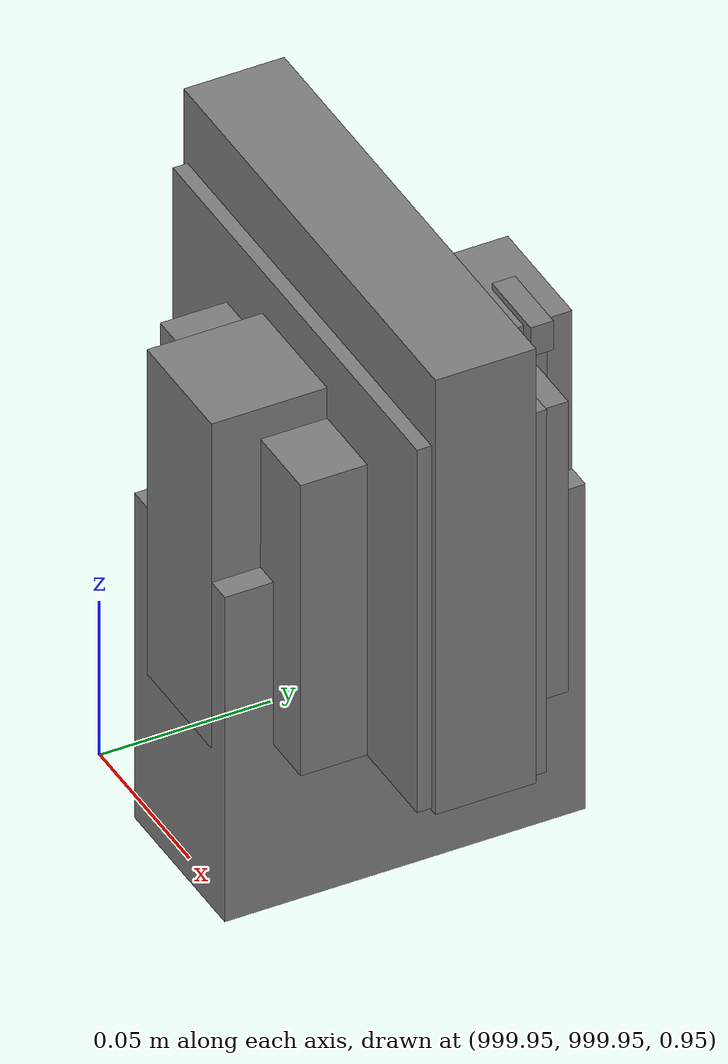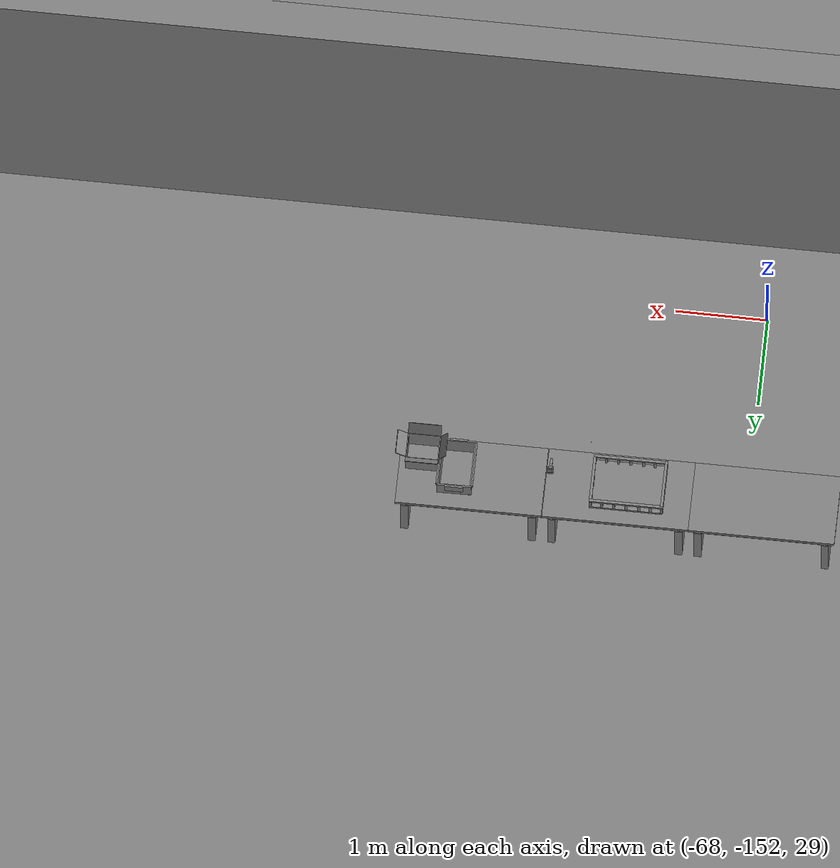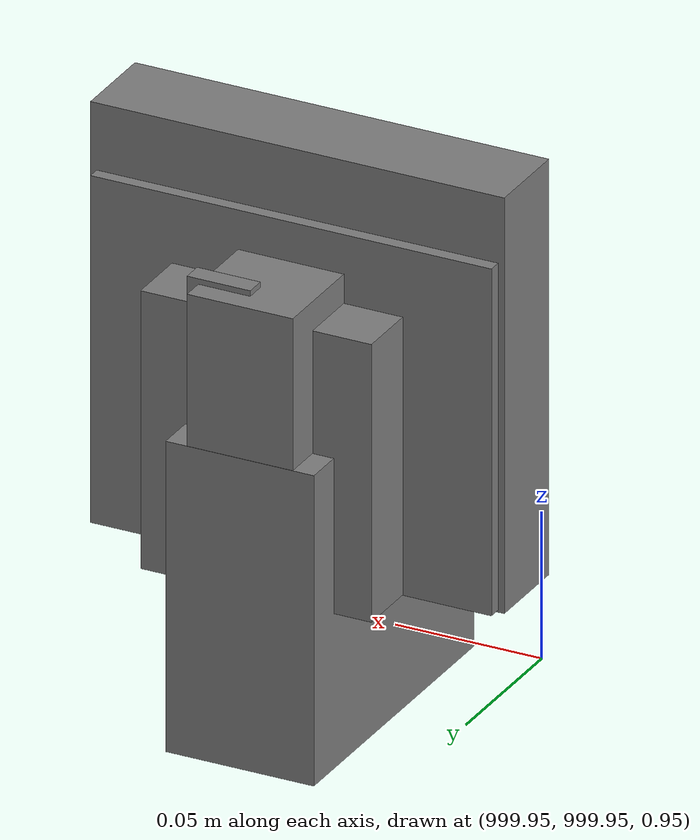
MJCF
<mujoco>
    <option gravity="0.000000000 0.000000000 -9.810000420" timestep="0.0049999999" integrator="implicitfast" density="1.225" viscosity="1.8000001e-05" noslip_iterations="10" iterations="100" sdf_iterations="50">
        <flag multiccd="disable"/>
    </option>
    <size memory="1000M"/>
    <compiler coordinate="local"/>
    <worldbody>
        <light cutoff="30" pos="0 1 1" dir="0 -1 -2"/>
        <light cutoff="30" pos="0 -1 1" dir="0 1 -2"/>
        <body pos="1000.000000000 1000.000000000 1.000000000" euler="0.000000000 0.000000000 180.000000000" name="openloong_gripper_2f85_fix_base_usda_wifi_box">
            <geom contype="1" conaffinity="1" density="1000" type="box" material="" rgba="0.500000000 0.500000000 0.500000000 1.000000000" solimp="0.899999976 0.949999988 0.001000000" friction="1.000000000 0.005000000 0.000100000" solref="0.020000000 1.000000000" margin="0" condim="3" group="0" pos="0.000000000 0.000000000 0.058978677" quat="0.000000000 0.000000047 0.000000000 1.000000000" size="0.068499997 0.018999999 0.059000000" name="openloong_gripper_2f85_fix_base_usda_geom_B0694550_C670_439E_BFC5_1AAE41967299"/>
            <freejoint name="openloong_gripper_2f85_fix_base_usda_wifi_box_joint"/>
            <site size="0.005000000 0.005000000 0.005000000" rgba="0.500000000 0.500000000 0.500000000 1.000000000" pos="0.000000000 0.000000000 0.000000000" quat="0.999961913 0.008726500 0.000000000 0.000000000" group="0" type="sphere" name="openloong_gripper_2f85_fix_base_usda_wifi_boxsite"/>
        </body>
        <body pos="1000.000000000 1000.000000000 1.000000000" euler="0.000000000 0.000000000 180.000000000" name="openloong_gripper_2f85_fix_base_usda_cpu_fan">
            <geom contype="1" conaffinity="1" density="1000" type="box" material="" rgba="0.500000000 0.500000000 0.500000000 1.000000000" solimp="0.899999976 0.949999988 0.001000000" friction="1.000000000 0.005000000 0.000100000" solref="0.020000000 1.000000000" margin="0" condim="3" group="0" pos="0.000000000 0.000000000 0.070034981" quat="0.000000000 0.000000000 0.000000000 1.000000000" size="0.070700005 0.014699999 0.070700005" name="openloong_gripper_2f85_fix_base_usda_geom_23734F7D_19C9_46E0_90CB_9951878BF3C8"/>
            <freejoint name="openloong_gripper_2f85_fix_base_usda_cpu_fan_joint"/>
            <site size="0.005000000 0.005000000 0.005000000" rgba="0.500000000 0.500000000 0.500000000 1.000000000" pos="0.000000000 0.000000000 0.000000000" quat="0.999961913 0.008726535 0.000000000 0.000000000" group="0" type="sphere" name="openloong_gripper_2f85_fix_base_usda_cpu_fancsite"/>
        </body>
        <body pos="-65.908111572 -149.634384155 31.167135239" euler="3.009442329 19.891588211 -2.253885984" mocap="true" name="spotlight3_SpotLight"/>
        <body pos="-66.242599487 -149.445373535 31.165855408" euler="139.940185547 15.645484924 46.539287567" mocap="true" name="spotlight5_SpotLight"/>
        <body pos="1000.000000000 1000.000000000 1.000000000" euler="0.000000000 0.000000000 180.000000000" name="openloong_gripper_2f85_fix_base_usda_battery_01">
            <geom contype="1" conaffinity="1" density="1000" type="box" material="" rgba="0.500000000 0.500000000 0.500000000 1.000000000" solimp="0.899999976 0.949999988 0.001000000" friction="1.000000000 0.005000000 0.000100000" solref="0.020000000 1.000000000" margin="0" condim="3" group="0" pos="-0.011123657 -0.041940309 0.101691343" quat="1.000000000 0.000000000 0.000000000 0.000000000" size="0.010800000 0.003375000 0.004725000" name="openloong_gripper_2f85_fix_base_usda_geom_4270D9AE_373F_48E9_86ED_9E89EC29A6E7"/>
            <geom contype="1" conaffinity="1" density="1000" type="box" material="" rgba="0.500000000 0.500000000 0.500000000 1.000000000" solimp="0.899999976 0.949999988 0.001000000" friction="1.000000000 0.005000000 0.000100000" solref="0.020000000 1.000000000" margin="0" condim="3" group="0" pos="-0.010876465 -0.044247437 0.047066893" quat="0.998702705 -0.050920475 0.000000000 0.000000000" size="0.009450001 0.002700000 0.024975000" name="openloong_gripper_2f85_fix_base_usda_geom_14D713CF_FE80_4813_8943_4420BCE80D38"/>
            <geom contype="1" conaffinity="1" density="1000" type="box" material="" rgba="0.500000000 0.500000000 0.500000000 1.000000000" solimp="0.899999976 0.949999988 0.001000000" friction="1.000000000 0.005000000 0.000100000" solref="0.020000000 1.000000000" margin="0" condim="3" group="0" pos="-0.001235962 -0.000659180 0.047381196" quat="1.000000000 0.000000000 0.000000000 0.000000000" size="0.039420001 0.039150000 0.047250003" name="openloong_gripper_2f85_fix_base_usda_geom_3D4AC454_4DFE_456B_AC64_41ECCF405430"/>
            <geom contype="1" conaffinity="1" density="1000" type="box" material="" rgba="0.500000000 0.500000000 0.500000000 1.000000000" solimp="0.899999976 0.949999988 0.001000000" friction="1.000000000 0.005000000 0.000100000" solref="0.020000000 1.000000000" margin="0" condim="3" group="0" pos="-0.010876465 -0.039138794 0.009851727" quat="1.000000000 0.000000000 0.000000000 0.000000000" size="0.009450001 0.010800000 0.013500000" name="openloong_gripper_2f85_fix_base_usda_geom_97387093_E00A_4A0E_A6B5_F7144C44C38A"/>
            <geom contype="1" conaffinity="1" density="1000" type="box" material="" rgba="0.500000000 0.500000000 0.500000000 1.000000000" solimp="0.899999976 0.949999988 0.001000000" friction="1.000000000 0.005000000 0.000100000" solref="0.020000000 1.000000000" margin="0" condim="3" group="0" pos="-0.010876465 -0.041528322 0.071508206" quat="1.000000000 0.000000000 0.000000000 0.000000000" size="0.009450001 0.002700000 0.027000001" name="openloong_gripper_2f85_fix_base_usda_geom_5CAC6218_40B5_409E_ABBE_AB8B729E60F3"/>
            <freejoint name="openloong_gripper_2f85_fix_base_usda_battery_01_joint"/>
            <site size="0.005000000 0.005000000 0.005000000" rgba="0.500000000 0.500000000 0.500000000 1.000000000" pos="0.000000000 0.000000000 0.000000000" quat="0.999961913 0.008726500 0.000000000 0.000000000" group="0" type="sphere" name="openloong_gripper_2f85_fix_base_usda_battery_01site"/>
        </body>
        <body pos="-66.291381836 -149.668609619 31.162714005" euler="167.506195068 82.811264038 60.717330933" mocap="true" name="spotlight1_SpotLight"/>
        <body pos="1000.000000000 999.999938965 1.000000000" euler="0.000000000 0.000000000 180.000000000" name="openloong_gripper_2f85_fix_base_usda_intelcore_i5">
            <geom contype="1" conaffinity="1" density="1000" type="box" material="" rgba="0.500000000 0.500000000 0.500000000 1.000000000" solimp="0.899999976 0.949999988 0.001000000" friction="1.000000000 0.005000000 0.000100000" solref="0.020000000 1.000000000" margin="0" condim="3" group="0" pos="0.000000000 0.000000000 0.051722717" quat="0.707106709 0.000000000 0.000000000 -0.707106769" size="0.052800000 0.018080002 0.052800000" name="openloong_gripper_2f85_fix_base_usda_geom_1675AF2B_E4B5_440E_8A5E_E155FF3AC23B"/>
            <freejoint name="openloong_gripper_2f85_fix_base_usda_intelcore_i5_joint"/>
            <site size="0.005000000 0.005000000 0.005000000" rgba="0.500000000 0.500000000 0.500000000 1.000000000" pos="0.000000000 0.000000000 0.000000000" quat="0.999961913 0.008726534 0.000000000 0.000000000" group="0" type="sphere" name="openloong_gripper_2f85_fix_base_usda_intelcore_i5site"/>
        </body>
        <body pos="1000.000000000 1000.000000000 1.000000000" euler="0.000011953 0.000005123 -179.999984741" name="openloong_gripper_2f85_fix_base_usda_intel_box">
            <geom contype="1" conaffinity="1" density="1000" type="box" material="" rgba="0.500000000 0.500000000 0.500000000 1.000000000" solimp="0.899999976 0.949999988 0.001000000" friction="1.000000000 0.005000000 0.000100000" solref="0.020000000 1.000000000" margin="0" condim="3" group="0" pos="0.000000000 -0.000067139 0.000082284" quat="0.707106709 0.000000225 0.000000253 0.707106650" size="0.052800003 0.025300000 0.052800003" name="openloong_gripper_2f85_fix_base_usda_geom_9343A7CD_ED3E_43DC_B439_BDF1943D0A03"/>
            <freejoint name="openloong_gripper_2f85_fix_base_usda_intel_box_joint"/>
            <site size="0.005000000 0.005000000 0.005000000" rgba="0.500000000 0.500000000 0.500000000 1.000000000" pos="0.000000000 0.000000000 0.000000000" quat="0.999961913 0.008726500 0.000000000 0.000000000" group="0" type="sphere" name="openloong_gripper_2f85_fix_base_usda_intel_boxsite"/>
        </body>
        <body pos="-64.866622925 -149.383972168 30.183746338" euler="89.999984741 89.999946594 0.000000000" name="openloong_gripper_2f85_fix_base_usda_bluebox_01">
            <geom contype="1" conaffinity="1" density="1000" type="box" material="" rgba="0.500000000 0.500000000 0.500000000 1.000000000" solimp="0.899999976 0.949999988 0.001000000" friction="1.000000000 0.005000000 0.000100000" solref="0.020000000 1.000000000" margin="0" condim="3" group="0" pos="0.276580811 0.187225342 0.000068665" quat="0.707106948 0.000077471 0.707106352 0.000077486" size="0.100000001 0.057999998 0.010000000" name="openloong_gripper_2f85_fix_base_usda_geom_D63B7562_4A83_4174_BB8A_ACF3CE3FA9BE"/>
            <geom contype="1" conaffinity="1" density="1000" type="box" material="" rgba="0.500000000 0.500000000 0.500000000 1.000000000" solimp="0.899999976 0.949999988 0.001000000" friction="1.000000000 0.005000000 0.000100000" solref="0.020000000 1.000000000" margin="0" condim="3" group="0" pos="0.000000000 0.002883911 0.000000000" quat="0.999999881 0.000000000 0.000000000 0.000000000" size="0.254000008 0.003000000 0.172000006" name="openloong_gripper_2f85_fix_base_usda_geom_21D3625E_F6BA_4D1A_8E0D_E968BCC6AC3D"/>
            <geom contype="1" conaffinity="1" density="1000" type="box" material="" rgba="0.500000000 0.500000000 0.500000000 1.000000000" solimp="0.899999976 0.949999988 0.001000000" friction="1.000000000 0.005000000 0.000100000" solref="0.020000000 1.000000000" margin="0" condim="3" group="0" pos="0.000000000 0.124874115 0.173484802" quat="0.999796331 0.020176515 -0.000000015 0.000000030" size="0.259999990 0.119999997 0.007000000" name="openloong_gripper_2f85_fix_base_usda_geom_6458A976_08C5_49E3_8B3C_2B103047B25B"/>
            <geom contype="1" conaffinity="1" density="1000" type="box" material="" rgba="0.500000000 0.500000000 0.500000000 1.000000000" solimp="0.899999976 0.949999988 0.001000000" friction="1.000000000 0.005000000 0.000100000" solref="0.020000000 1.000000000" margin="0" condim="3" group="0" pos="0.000000000 0.124874115 -0.173469543" quat="0.999796331 -0.020176545 -0.000000015 0.000000000" size="0.259999990 0.119999997 0.007000000" name="openloong_gripper_2f85_fix_base_usda_geom_7BE54D0F_AA25_4875_940C_BA07585E72DB"/>
            <geom contype="1" conaffinity="1" density="1000" type="box" material="" rgba="0.500000000 0.500000000 0.500000000 1.000000000" solimp="0.899999976 0.949999988 0.001000000" friction="1.000000000 0.005000000 0.000100000" solref="0.020000000 1.000000000" margin="0" condim="3" group="0" pos="0.000000000 0.214008331 0.188980103" quat="0.999912977 0.013176724 0.000000015 0.000000000" size="0.259999990 0.029999999 0.012500000" name="openloong_gripper_2f85_fix_base_usda_geom_82BE315B_01EE_4F7A_B711_E46ACEDAC347"/>
            <geom contype="1" conaffinity="1" density="1000" type="box" material="" rgba="0.500000000 0.500000000 0.500000000 1.000000000" solimp="0.899999976 0.949999988 0.001000000" friction="1.000000000 0.005000000 0.000100000" solref="0.020000000 1.000000000" margin="0" condim="3" group="0" pos="-0.258361816 0.125289917 0.001876831" quat="0.702796936 -0.020792112 0.710783124 0.020769298" size="0.189999998 0.119999997 0.009000000" name="openloong_gripper_2f85_fix_base_usda_geom_6C5CAC02_4384_4B0B_A70D_59FAB26A655A"/>
            <geom contype="1" conaffinity="1" density="1000" type="box" material="" rgba="0.500000000 0.500000000 0.500000000 1.000000000" solimp="0.899999976 0.949999988 0.001000000" friction="1.000000000 0.005000000 0.000100000" solref="0.020000000 1.000000000" margin="0" condim="3" group="0" pos="0.000000000 0.214008331 -0.188980103" quat="0.999912977 -0.013176769 0.000000030 0.000000015" size="0.259999990 0.029999999 0.012500000" name="openloong_gripper_2f85_fix_base_usda_geom_AC50564A_E765_44B1_9040_134C59F01171"/>
            <geom contype="1" conaffinity="1" density="1000" type="box" material="" rgba="0.500000000 0.500000000 0.500000000 1.000000000" solimp="0.899999976 0.949999988 0.001000000" friction="1.000000000 0.005000000 0.000100000" solref="0.020000000 1.000000000" margin="0" condim="3" group="0" pos="-0.276611328 0.187225342 0.000068665" quat="0.707106650 0.000077441 0.707106709 0.000077456" size="0.100000001 0.057999998 0.010000000" name="openloong_gripper_2f85_fix_base_usda_geom_57015FB9_CD51_47B5_9114_120BBCF1EE0A"/>
            <geom contype="1" conaffinity="1" density="1000" type="box" material="" rgba="0.500000000 0.500000000 0.500000000 1.000000000" solimp="0.899999976 0.949999988 0.001000000" friction="1.000000000 0.005000000 0.000100000" solref="0.020000000 1.000000000" margin="0" condim="3" group="0" pos="0.258331299 0.125289917 0.001876831" quat="0.702851415 0.018856421 0.710823774 -0.019329369" size="0.189999998 0.119999997 0.009000000" name="openloong_gripper_2f85_fix_base_usda_geom_F7D94218_7427_406C_9E74_34B72E9DE686"/>
            <freejoint name="openloong_gripper_2f85_fix_base_usda_bluebox_01_joint"/>
            <site size="0.005000000 0.005000000 0.005000000" rgba="0.500000000 0.500000000 0.500000000 1.000000000" pos="0.000000000 0.000000000 0.000000000" quat="0.999961913 0.008726534 0.000000000 0.000000000" group="0" type="sphere" name="openloong_gripper_2f85_fix_base_usda_bluebox_01site"/>
        </body>
        <body pos="-64.496299744 -149.491867065 30.235729218" euler="0.000000000 0.000000000 89.999946594" name="openloong_gripper_2f85_fix_base_usda_cardboardbox_01">
            <geom contype="1" conaffinity="1" density="1000" type="box" material="" rgba="0.500000000 0.500000000 0.500000000 1.000000000" solimp="0.899999976 0.949999988 0.001000000" friction="1.000000000 0.005000000 0.000100000" solref="0.020000000 1.000000000" margin="0" condim="3" group="0" pos="-0.003166199 -0.004086494 0.005052090" quat="1.000000000 0.000000000 0.000000000 0.000000000" size="0.142499998 0.177500010 0.005000000" name="openloong_gripper_2f85_fix_base_usda_geom_2877580E_722A_4D7D_A557_655E73CFD144"/>
            <geom contype="1" conaffinity="1" density="1000" type="box" material="" rgba="0.500000000 0.500000000 0.500000000 1.000000000" solimp="0.899999976 0.949999988 0.001000000" friction="1.000000000 0.005000000 0.000100000" solref="0.020000000 1.000000000" margin="0" condim="3" group="0" pos="-0.003166199 0.170316696 0.150570869" quat="1.000000000 0.000000000 0.000000000 0.000000000" size="0.142499998 0.005000000 0.149999991" name="openloong_gripper_2f85_fix_base_usda_geom_181D27D5_D980_46F6_AB10_A9EA95690E54"/>
            <geom contype="1" conaffinity="1" density="1000" type="box" material="" rgba="0.500000000 0.500000000 0.500000000 1.000000000" solimp="0.899999976 0.949999988 0.001000000" friction="1.000000000 0.005000000 0.000100000" solref="0.020000000 1.000000000" margin="0" condim="3" group="0" pos="-0.147399902 -0.005307198 0.150570869" quat="1.000000000 0.000000000 0.000000000 0.000000000" size="0.005000000 0.177500010 0.149999991" name="openloong_gripper_2f85_fix_base_usda_geom_D21D87D3_B152_4193_B6FD_2ACAE3DA0A4B"/>
            <geom contype="1" conaffinity="1" density="1000" type="box" material="" rgba="0.500000000 0.500000000 0.500000000 1.000000000" solimp="0.899999976 0.949999988 0.001000000" friction="1.000000000 0.005000000 0.000100000" solref="0.020000000 1.000000000" margin="0" condim="3" group="0" pos="0.140275955 -0.005307198 0.150570869" quat="1.000000000 0.000000000 0.000000000 0.000000000" size="0.005000000 0.177500010 0.149999991" name="openloong_gripper_2f85_fix_base_usda_geom_CC26322C_BD02_462B_AC68_208855F62D5D"/>
            <geom contype="1" conaffinity="1" density="1000" type="box" material="" rgba="0.500000000 0.500000000 0.500000000 1.000000000" solimp="0.899999976 0.949999988 0.001000000" friction="1.000000000 0.005000000 0.000100000" solref="0.020000000 1.000000000" margin="0" condim="3" group="0" pos="-0.003166199 -0.181550980 0.150570869" quat="1.000000000 0.000000000 0.000000000 0.000000000" size="0.142499998 0.005000000 0.149999991" name="openloong_gripper_2f85_fix_base_usda_geom_9C356027_2124_45E8_BEE6_3E8A8C0758A1"/>
            <freejoint name="openloong_gripper_2f85_fix_base_usda_cardboardbox_01_joint"/>
            <site size="0.005000000 0.005000000 0.005000000" rgba="0.500000000 0.500000000 0.500000000 1.000000000" pos="0.000000000 0.000000000 0.000000000" quat="0.999961913 0.008726535 0.000000000 0.000000000" group="0" type="sphere" name="openloong_gripper_2f85_fix_base_usda_site_D22ECB34_3A78_4B4E_8BC5_BADED8C6FF3D"/>
            <body pos="0.139160156 -0.004048347 0.301930904" euler="-179.999954224 49.383502960 179.999954224" name="openloong_gripper_2f85_fix_base_usda_A1_006">
                <geom contype="1" conaffinity="1" density="1000" type="box" material="" rgba="0.500000000 0.500000000 0.500000000 1.000000000" solimp="0.899999976 0.949999988 0.001000000" friction="1.000000000 0.005000000 0.000100000" solref="0.020000000 1.000000000" margin="0" condim="3" group="0" pos="-0.071587563 0.000009537 0.001745224" quat="0.999999881 0.000000000 0.000000000 0.000000000" size="0.071249999 0.179999992 0.002500000" name="openloong_gripper_2f85_fix_base_usda_geom_781A67CD_120D_4570_B71D_23287A69027E"/>
                <joint armature="0" stiffness="0.07" damping="0.0099999998" axis="0.000000 1.000000 0.000000" type="hinge" name="openloong_gripper_2f85_fix_base_usda_A1_006"/>
            </body>
            <body pos="-0.145902634 -0.004086494 0.301938057" euler="-180.000000000 -60.000011444 -180.000000000" name="openloong_gripper_2f85_fix_base_usda_A2_006">
                <geom contype="1" conaffinity="1" density="1000" type="box" material="" rgba="0.500000000 0.500000000 0.500000000 1.000000000" solimp="0.899999976 0.949999988 0.001000000" friction="1.000000000 0.005000000 0.000100000" solref="0.020000000 1.000000000" margin="0" condim="3" group="0" pos="0.071268082 0.000009537 0.002717972" quat="0.000002921 0.000000000 -0.000000030 0.999999881" size="0.071249999 0.179999992 0.002500000" name="openloong_gripper_2f85_fix_base_usda_geom_D65CDE9F_7706_45BB_B274_BED62CE90824"/>
                <joint armature="0" stiffness="0.07" damping="0.0099999998" axis="0.000000 1.000000 0.000000" type="hinge" name="openloong_gripper_2f85_fix_base_usda_A2_006"/>
            </body>
            <body pos="-0.003385544 0.175991058 0.301930904" euler="-125.858116150 -0.000004561 0.000002331" name="openloong_gripper_2f85_fix_base_usda_B2_006">
                <geom contype="1" conaffinity="1" density="1000" type="box" material="" rgba="0.500000000 0.500000000 0.500000000 1.000000000" solimp="0.899999976 0.949999988 0.001000000" friction="1.000000000 0.005000000 0.000100000" solref="0.020000000 1.000000000" margin="0" condim="3" group="0" pos="0.000009537 -0.070939064 -0.002470016" quat="0.999614120 0.027776197 -0.000000015 0.000000030" size="0.137500003 0.064999998 0.005000000" name="openloong_gripper_2f85_fix_base_usda_geom_6567F0A2_5188_4225_A25A_F23E426132F2"/>
                <joint armature="0" stiffness="0.07" damping="0.0099999998" axis="1.000000 0.000000 0.000000" type="hinge" name="openloong_gripper_2f85_fix_base_usda_B2_006"/>
            </body>
            <body pos="-0.003385544 -0.184140205 0.301938057" euler="147.805557251 0.000000000 0.000000000" name="openloong_gripper_2f85_fix_base_usda_B1_006">
                <geom contype="1" conaffinity="1" density="1000" type="box" material="" rgba="0.500000000 0.500000000 0.500000000 1.000000000" solimp="0.899999976 0.949999988 0.001000000" friction="1.000000000 0.005000000 0.000100000" solref="0.020000000 1.000000000" margin="0" condim="3" group="0" pos="-0.000028610 0.070202351 -0.002703667" quat="0.999614179 -0.027776167 0.000000000 0.000000000" size="0.137500003 0.064999998 0.005000000" name="openloong_gripper_2f85_fix_base_usda_geom_ED83E7E8_9096_49E9_9BE4_0482078FD588"/>
                <joint armature="0" stiffness="0.07" damping="0.0099999998" axis="1.000000 0.000000 0.000000" type="hinge" name="openloong_gripper_2f85_fix_base_usda_B1_006"/>
            </body>
        </body>
        <body pos="-65.882858276 -149.481979370 30.229999542" euler="-64.487716675 0.000000000 0.000000000" name="openloong_gripper_2f85_fix_base_usda_Barcode">
            <geom contype="1" conaffinity="1" density="1000" type="box" material="" rgba="0.500000000 0.500000000 0.500000000 1.000000000" solimp="0.899999976 0.949999988 0.001000000" friction="1.000000000 0.005000000 0.000100000" solref="0.020000000 1.000000000" margin="0" condim="3" group="0" pos="0.000000000 0.013038635 0.001419067" quat="0.000000000 0.000000000 0.000000000 1.000000119" size="0.034000002 0.010000000 0.017999999" name="openloong_gripper_2f85_fix_base_usda_geom_288E8404_9B37_4B1A_A39F_886FD7F6AE93"/>
            <geom contype="1" conaffinity="1" density="1000" type="box" material="" rgba="0.500000000 0.500000000 0.500000000 1.000000000" solimp="0.899999976 0.949999988 0.001000000" friction="1.000000000 0.005000000 0.000100000" solref="0.020000000 1.000000000" margin="0" condim="3" group="0" pos="0.000000000 -0.035301208 -0.007095337" quat="0.000000000 0.000000000 -0.043619365 0.999048233" size="0.028999999 0.010000000 0.020000000" name="openloong_gripper_2f85_fix_base_usda_geom_428AA16D_10F1_4986_8E9B_D7377168215E"/>
            <geom contype="1" conaffinity="1" density="1000" type="box" material="" rgba="0.500000000 0.500000000 0.500000000 1.000000000" solimp="0.899999976 0.949999988 0.001000000" friction="1.000000000 0.005000000 0.000100000" solref="0.020000000 1.000000000" margin="0" condim="3" group="0" pos="0.000000000 -0.043411255 -0.011749268" quat="0.922262907 0.386563420 0.000000000 0.000000000" size="0.026000001 0.010000000 0.020000000" name="openloong_gripper_2f85_fix_base_usda_geom_C2394EDF_2D6C_4C7E_BDD7_F33E475F57B0"/>
            <geom contype="1" conaffinity="1" density="1000" type="box" material="" rgba="0.500000000 0.500000000 0.500000000 1.000000000" solimp="0.899999976 0.949999988 0.001000000" friction="1.000000000 0.005000000 0.000100000" solref="0.020000000 1.000000000" margin="0" condim="3" group="0" pos="0.000000000 -0.016967773 -0.031860352" quat="0.000000000 0.000000000 0.000000000 1.000000119" size="0.008000000 0.010000000 0.013000000" name="openloong_gripper_2f85_fix_base_usda_geom_5C9E31B3_2A81_45B8_9D97_2C8E4610178E"/>
            <geom contype="1" conaffinity="1" density="1000" type="box" material="" rgba="0.500000000 0.500000000 0.500000000 1.000000000" solimp="0.899999976 0.949999988 0.001000000" friction="1.000000000 0.005000000 0.000100000" solref="0.020000000 1.000000000" margin="0" condim="3" group="0" pos="0.000000000 -0.001869202 0.000312805" quat="0.953716993 0.300705761 0.000000000 0.000000000" size="0.032000002 0.010000000 0.018999999" name="openloong_gripper_2f85_fix_base_usda_geom_AC85FDD8_EEA5_4614_B32D_297BBB6A32F1"/>
            <geom contype="1" conaffinity="1" density="1000" type="box" material="" rgba="0.500000000 0.500000000 0.500000000 1.000000000" solimp="0.899999976 0.949999988 0.001000000" friction="1.000000000 0.005000000 0.000100000" solref="0.020000000 1.000000000" margin="0" condim="3" group="0" pos="0.000000000 -0.019531250 -0.003173828" quat="0.953716993 0.300705761 0.000000000 0.000000000" size="0.030999999 0.010000000 0.020000000" name="openloong_gripper_2f85_fix_base_usda_geom_8D58F677_2645_4857_8B11_415395ADF2BB"/>
            <geom contype="1" conaffinity="1" density="1000" type="box" material="" rgba="0.500000000 0.500000000 0.500000000 1.000000000" solimp="0.899999976 0.949999988 0.001000000" friction="1.000000000 0.005000000 0.000100000" solref="0.020000000 1.000000000" margin="0" condim="3" group="0" pos="0.000000000 -0.035301208 -0.007095337" quat="0.953716993 0.300705761 0.000000000 0.000000000" size="0.028999999 0.010000000 0.020000000" name="openloong_gripper_2f85_fix_base_usda_geom_BE904AE0_9ABC_4BF6_A16D_5DF5DAC0D365"/>
            <geom contype="1" conaffinity="1" density="1000" type="box" material="" rgba="0.500000000 0.500000000 0.500000000 1.000000000" solimp="0.899999976 0.949999988 0.001000000" friction="1.000000000 0.005000000 0.000100000" solref="0.020000000 1.000000000" margin="0" condim="3" group="0" pos="0.000000000 -0.042617798 -0.071121216" quat="0.000000000 0.000000000 0.000000000 1.000000119" size="0.013000000 0.021000000 0.059999999" name="openloong_gripper_2f85_fix_base_usda_geom_A34840C5_C582_4108_B180_FBE2726665A6"/>
            <freejoint name="openloong_gripper_2f85_fix_base_usda_Barcode_joint"/>
            <site size="0.005000000 0.005000000 0.005000000" rgba="0.500000000 0.500000000 0.500000000 1.000000000" pos="0.000000000 0.000000000 0.000000000" quat="1.000000000 0.000000000 0.000000000 0.000000000" group="0" type="sphere" name="openloong_gripper_2f85_fix_base_usda_Barcode_site"/>
        </body>
        <body pos="-66.745018005 -149.392349243 30.184000015" euler="0.000000000 0.000000000 89.999946594" name="[22331454903536]_Basket_01">
            <geom contype="1" conaffinity="1" density="1000" type="box" material="" rgba="0.500000000 0.500000000 0.500000000 1.000000000" solimp="0.899999976 0.949999988 0.001000000" friction="1.000000000 0.005000000 0.000100000" solref="0.020000000 1.000000000" margin="0" condim="3" group="0" pos="-0.052425385 0.389207840 0.089787483" quat="0.707107008 0.000000000 0.000000000 0.707106411" size="0.014249999 0.014249999 0.059999999" name="[22331454903536]_geom_D303DEF3_33A3_4ABF_8FD2_9C8ACB932E75"/>
            <geom contype="1" conaffinity="1" density="1000" type="box" material="" rgba="0.500000000 0.500000000 0.500000000 1.000000000" solimp="0.899999976 0.949999988 0.001000000" friction="1.000000000 0.005000000 0.000100000" solref="0.020000000 1.000000000" margin="0" condim="3" group="0" pos="0.264015198 -0.133043289 0.089787483" quat="0.707107008 0.000000000 0.000000000 0.707106411" size="0.014249999 0.014249999 0.059999999" name="[22331454903536]_geom_410AED3F_716F_4F67_98DE_BE86B60A4B22"/>
            <geom contype="1" conaffinity="1" density="1000" type="box" material="" rgba="0.500000000 0.500000000 0.500000000 1.000000000" solimp="0.899999976 0.949999988 0.001000000" friction="1.000000000 0.005000000 0.000100000" solref="0.020000000 1.000000000" margin="0" condim="3" group="0" pos="-0.264015198 -0.265548706 0.089793205" quat="0.707107008 0.000000000 0.000000000 0.707106411" size="0.014249999 0.014249999 0.059999999" name="[22331454903536]_geom_9DB4C38F_B162_484B_BF95_BB2A06EF51E8"/>
            <geom contype="1" conaffinity="1" density="1000" type="box" material="" rgba="0.500000000 0.500000000 0.500000000 1.000000000" solimp="0.899999976 0.949999988 0.001000000" friction="1.000000000 0.005000000 0.000100000" solref="0.020000000 1.000000000" margin="0" condim="3" group="0" pos="-0.160263062 -0.389322281 0.089793205" quat="0.707107008 0.000000000 0.000000000 0.707106411" size="0.014249999 0.014249999 0.059999999" name="[22331454903536]_geom_BE9A8C34_54E6_4DFC_9910_6CC964F56971"/>
            <geom contype="1" conaffinity="1" density="1000" type="box" material="" rgba="0.500000000 0.500000000 0.500000000 1.000000000" solimp="0.899999976 0.949999988 0.001000000" friction="1.000000000 0.005000000 0.000100000" solref="0.020000000 1.000000000" margin="0" condim="3" group="0" pos="0.162265778 -0.389322281 0.089787483" quat="0.707107008 0.000000000 0.000000000 0.707106411" size="0.014249999 0.014249999 0.059999999" name="[22331454903536]_geom_25B02ED8_DEDB_40BB_A17B_61E6243FDDD9"/>
            <geom contype="1" conaffinity="1" density="1000" type="box" material="" rgba="0.500000000 0.500000000 0.500000000 1.000000000" solimp="0.899999976 0.949999988 0.001000000" friction="1.000000000 0.005000000 0.000100000" solref="0.020000000 1.000000000" margin="0" condim="3" group="0" pos="0.264015198 0.389207840 0.089787483" quat="0.707107008 0.000000000 0.000000000 0.707106411" size="0.014249999 0.014249999 0.059999999" name="[22331454903536]_geom_94C6967F_2DF7_40F9_BFBA_E7E1D5091AB6"/>
            <geom contype="1" conaffinity="1" density="1000" type="box" material="" rgba="0.500000000 0.500000000 0.500000000 1.000000000" solimp="0.899999976 0.949999988 0.001000000" friction="1.000000000 0.005000000 0.000100000" solref="0.020000000 1.000000000" margin="0" condim="3" group="0" pos="-0.264015198 -0.133043289 0.089793205" quat="0.707107008 0.000000000 0.000000000 0.707106411" size="0.014249999 0.014249999 0.059999999" name="[22331454903536]_geom_3F2CCB3D_11E0_46E2_BDF9_4347DE2480E3"/>
            <geom contype="1" conaffinity="1" density="1000" type="box" material="" rgba="0.500000000 0.500000000 0.500000000 1.000000000" solimp="0.899999976 0.949999988 0.001000000" friction="1.000000000 0.005000000 0.000100000" solref="0.020000000 1.000000000" margin="0" condim="3" group="0" pos="-0.264026642 0.269256592 0.089793205" quat="0.707107008 0.000000000 0.000000000 0.707106411" size="0.014249999 0.014249999 0.059999999" name="[22331454903536]_geom_E2B4353A_3DC5_4640_8185_030B63C980F8"/>
            <geom contype="1" conaffinity="1" density="1000" type="box" material="" rgba="0.500000000 0.500000000 0.500000000 1.000000000" solimp="0.899999976 0.949999988 0.001000000" friction="1.000000000 0.005000000 0.000100000" solref="0.020000000 1.000000000" margin="0" condim="3" group="0" pos="0.054462433 0.389207840 0.089787483" quat="0.707107008 0.000000000 0.000000000 0.707106411" size="0.014249999 0.014249999 0.059999999" name="[22331454903536]_geom_D21BF37D_1D76_408C_9E76_5F843C61D224"/>
            <geom contype="1" conaffinity="1" density="1000" type="box" material="" rgba="0.500000000 0.500000000 0.500000000 1.000000000" solimp="0.899999976 0.949999988 0.001000000" friction="1.000000000 0.005000000 0.000100000" solref="0.020000000 1.000000000" margin="0" condim="3" group="0" pos="0.054462433 -0.389322281 0.089787483" quat="0.707107008 0.000000000 0.000000000 0.707106411" size="0.014249999 0.014249999 0.059999999" name="[22331454903536]_geom_C1282DA8_C17C_4FE1_B4F8_4078376C842C"/>
            <geom contype="1" conaffinity="1" density="1000" type="box" material="" rgba="0.500000000 0.500000000 0.500000000 1.000000000" solimp="0.899999976 0.949999988 0.001000000" friction="1.000000000 0.005000000 0.000100000" solref="0.020000000 1.000000000" margin="0" condim="3" group="0" pos="0.264015198 0.269256592 0.089793205" quat="0.707107008 0.000000000 0.000000000 0.707106411" size="0.014249999 0.014249999 0.059999999" name="[22331454903536]_geom_4412EF84_133B_4E3F_995E_9FC5C9D36A2C"/>
            <geom contype="1" conaffinity="1" density="1000" type="box" material="" rgba="0.500000000 0.500000000 0.500000000 1.000000000" solimp="0.899999976 0.949999988 0.001000000" friction="1.000000000 0.005000000 0.000100000" solref="0.020000000 1.000000000" margin="0" condim="3" group="0" pos="0.264015198 -0.389322281 0.089787483" quat="0.707107008 0.000000000 0.000000000 0.707106411" size="0.014249999 0.014249999 0.059999999" name="[22331454903536]_geom_2E32C6BF_E6D9_4DC9_B3DA_9502B966C514"/>
            <geom contype="1" conaffinity="1" density="1000" type="box" material="" rgba="0.500000000 0.500000000 0.500000000 1.000000000" solimp="0.899999976 0.949999988 0.001000000" friction="1.000000000 0.005000000 0.000100000" solref="0.020000000 1.000000000" margin="0" condim="3" group="0" pos="0.000000000 0.000000000 0.015998840" quat="0.707107008 0.000000000 0.000000000 0.707106411" size="0.403499991 0.279000014 0.015750000" name="[22331454903536]_geom_357EC264_F9C5_4AA6_9309_58049DE260FA"/>
            <geom contype="1" conaffinity="1" density="1000" type="box" material="" rgba="0.500000000 0.500000000 0.500000000 1.000000000" solimp="0.899999976 0.949999988 0.001000000" friction="1.000000000 0.005000000 0.000100000" solref="0.020000000 1.000000000" margin="0" condim="3" group="0" pos="0.000000000 -0.389476776 0.163619041" quat="0.707107008 0.000000000 0.000000000 0.707106411" size="0.015000000 0.277500004 0.015750000" name="[22331454903536]_geom_15AE0643_2A71_4777_A6BF_33D4535B955E"/>
            <geom contype="1" conaffinity="1" density="1000" type="box" material="" rgba="0.500000000 0.500000000 0.500000000 1.000000000" solimp="0.899999976 0.949999988 0.001000000" friction="1.000000000 0.005000000 0.000100000" solref="0.020000000 1.000000000" margin="0" condim="3" group="0" pos="0.162265778 0.389207840 0.089787483" quat="0.707107008 0.000000000 0.000000000 0.707106411" size="0.014249999 0.014249999 0.059999999" name="[22331454903536]_geom_CFA2D1B8_8048_4C6E_8A8B_6416B0F90C55"/>
            <geom contype="1" conaffinity="1" density="1000" type="box" material="" rgba="0.500000000 0.500000000 0.500000000 1.000000000" solimp="0.899999976 0.949999988 0.001000000" friction="1.000000000 0.005000000 0.000100000" solref="0.020000000 1.000000000" margin="0" condim="3" group="0" pos="0.000000000 0.389471054 0.163619041" quat="0.707107008 0.000000000 0.000000000 0.707106411" size="0.015000000 0.277500004 0.015750000" name="[22331454903536]_geom_AA202E35_17E3_4311_9188_D63BBEF01D94"/>
            <geom contype="1" conaffinity="1" density="1000" type="box" material="" rgba="0.500000000 0.500000000 0.500000000 1.000000000" solimp="0.899999976 0.949999988 0.001000000" friction="1.000000000 0.005000000 0.000100000" solref="0.020000000 1.000000000" margin="0" condim="3" group="0" pos="-0.263511658 0.000000000 0.163619041" quat="0.707107008 0.000000000 0.000000000 0.707106411" size="0.403499991 0.015000000 0.015750000" name="[22331454903536]_geom_F37CABA7_57E5_4BB7_BB62_82F3A8918E00"/>
            <geom contype="1" conaffinity="1" density="1000" type="box" material="" rgba="0.500000000 0.500000000 0.500000000 1.000000000" solimp="0.899999976 0.949999988 0.001000000" friction="1.000000000 0.005000000 0.000100000" solref="0.020000000 1.000000000" margin="0" condim="3" group="0" pos="-0.264015198 0.141334534 0.089793205" quat="0.707107008 0.000000000 0.000000000 0.707106411" size="0.014249999 0.014249999 0.059999999" name="[22331454903536]_geom_6735B0AB_E2DD_4BCC_BDA8_64FAD74E2FD3"/>
            <geom contype="1" conaffinity="1" density="1000" type="box" material="" rgba="0.500000000 0.500000000 0.500000000 1.000000000" solimp="0.899999976 0.949999988 0.001000000" friction="1.000000000 0.005000000 0.000100000" solref="0.020000000 1.000000000" margin="0" condim="3" group="0" pos="0.264015198 -0.265548706 0.089787483" quat="0.707107008 0.000000000 0.000000000 0.707106411" size="0.014249999 0.014249999 0.059999999" name="[22331454903536]_geom_CFCBD791_4865_4243_B9C8_E46D8720B6D1"/>
            <geom contype="1" conaffinity="1" density="1000" type="box" material="" rgba="0.500000000 0.500000000 0.500000000 1.000000000" solimp="0.899999976 0.949999988 0.001000000" friction="1.000000000 0.005000000 0.000100000" solref="0.020000000 1.000000000" margin="0" condim="3" group="0" pos="-0.160263062 0.389207840 0.089787483" quat="0.707107008 0.000000000 0.000000000 0.707106411" size="0.014249999 0.014249999 0.059999999" name="[22331454903536]_geom_9C29327D_E7B8_487A_86A2_EA1D4192F913"/>
            <geom contype="1" conaffinity="1" density="1000" type="box" material="" rgba="0.500000000 0.500000000 0.500000000 1.000000000" solimp="0.899999976 0.949999988 0.001000000" friction="1.000000000 0.005000000 0.000100000" solref="0.020000000 1.000000000" margin="0" condim="3" group="0" pos="-0.052425385 -0.389322281 0.089787483" quat="0.707107008 0.000000000 0.000000000 0.707106411" size="0.014249999 0.014249999 0.059999999" name="[22331454903536]_geom_3B35228F_5657_4A58_B0AA_7A569A36142B"/>
            <geom contype="1" conaffinity="1" density="1000" type="box" material="" rgba="0.500000000 0.500000000 0.500000000 1.000000000" solimp="0.899999976 0.949999988 0.001000000" friction="1.000000000 0.005000000 0.000100000" solref="0.020000000 1.000000000" margin="0" condim="3" group="0" pos="-0.264026642 -0.389322281 0.089793205" quat="0.707107008 0.000000000 0.000000000 0.707106411" size="0.014249999 0.014249999 0.059999999" name="[22331454903536]_geom_F2F1B4CE_0A69_4EEA_BEFF_529D4024E079"/>
            <geom contype="1" conaffinity="1" density="1000" type="box" material="" rgba="0.500000000 0.500000000 0.500000000 1.000000000" solimp="0.899999976 0.949999988 0.001000000" friction="1.000000000 0.005000000 0.000100000" solref="0.020000000 1.000000000" margin="0" condim="3" group="0" pos="0.264015198 0.141334534 0.089787483" quat="0.707107008 0.000000000 0.000000000 0.707106411" size="0.014249999 0.014249999 0.059999999" name="[22331454903536]_geom_1E85E650_1818_485B_BA73_5582622A3C31"/>
            <geom contype="1" conaffinity="1" density="1000" type="box" material="" rgba="0.500000000 0.500000000 0.500000000 1.000000000" solimp="0.899999976 0.949999988 0.001000000" friction="1.000000000 0.005000000 0.000100000" solref="0.020000000 1.000000000" margin="0" condim="3" group="0" pos="-0.264015198 0.389207840 0.089793205" quat="0.707107008 0.000000000 0.000000000 0.707106411" size="0.014249999 0.014249999 0.059999999" name="[22331454903536]_geom_16B20CF6_F740_4F4D_89D3_464C98094B20"/>
            <geom contype="1" conaffinity="1" density="1000" type="box" material="" rgba="0.500000000 0.500000000 0.500000000 1.000000000" solimp="0.899999976 0.949999988 0.001000000" friction="1.000000000 0.005000000 0.000100000" solref="0.020000000 1.000000000" margin="0" condim="3" group="0" pos="0.264015198 0.004480362 0.089787483" quat="0.707107008 0.000000000 0.000000000 0.707106411" size="0.014249999 0.014249999 0.059999999" name="[22331454903536]_geom_84E4BC9B_C0EF_486C_AEF4_113097181135"/>
            <geom contype="1" conaffinity="1" density="1000" type="box" material="" rgba="0.500000000 0.500000000 0.500000000 1.000000000" solimp="0.899999976 0.949999988 0.001000000" friction="1.000000000 0.005000000 0.000100000" solref="0.020000000 1.000000000" margin="0" condim="3" group="0" pos="0.263694763 -0.000011444 0.163619041" quat="0.707107008 0.000000000 0.000000000 0.707106411" size="0.403499991 0.015000000 0.015750000" name="[22331454903536]_geom_9EB4A7B2_2A22_4E1A_842B_5AAF23832B40"/>
            <geom contype="1" conaffinity="1" density="1000" type="box" material="" rgba="0.500000000 0.500000000 0.500000000 1.000000000" solimp="0.899999976 0.949999988 0.001000000" friction="1.000000000 0.005000000 0.000100000" solref="0.020000000 1.000000000" margin="0" condim="3" group="0" pos="-0.264015198 0.004480362 0.089793205" quat="0.707107008 0.000000000 0.000000000 0.707106411" size="0.014249999 0.014249999 0.059999999" name="[22331454903536]_geom_A078F5DD_2CE7_492A_AAE6_FAA89650D3D9"/>
            <freejoint name="[22331454903536]_joint_4D7142D3_EA69_4F5E_B08C_1950A742CF42"/>
        </body>
        <body pos="0.000000000 0.000000000 0.000000000" euler="0.000000000 0.000000000 0.000000000" name="Static Objects_Static Objects">
            <geom contype="1" conaffinity="1" density="1000" type="box" material="" rgba="0.500000000 0.500000000 0.500000000 1.000000000" solimp="0.899999976 0.949999988 0.001000000" friction="1.000000000 0.005000000 0.000100000" solref="0.020000000 1.000000000" margin="0" condim="3" group="0" pos="-67.544113159 -149.365814209 29.727830887" quat="0.500000417 0.499999970 0.499999553 0.499999970" size="0.381000012 0.319999993 0.041000001" name="Static Objects_geom_71D56C68_F16B_49D0_98F2_BBFF55791575"/>
            <geom contype="1" conaffinity="1" density="1000" type="box" material="" rgba="0.500000000 0.500000000 0.500000000 1.000000000" solimp="0.899999976 0.949999988 0.001000000" friction="1.000000000 0.005000000 0.000100000" solref="0.020000000 1.000000000" margin="0" condim="3" group="0" pos="-68.239501953 -149.365814209 30.086868286" quat="0.500000417 0.499999970 0.499999553 0.499999970" size="0.370999992 0.039500002 0.745000005" name="Static Objects_geom_18F1BCC0_3A0B_4D6B_8878_5466266AD0A7"/>
            <geom contype="1" conaffinity="1" density="1000" type="box" material="" rgba="0.500000000 0.500000000 0.500000000 1.000000000" solimp="0.899999976 0.949999988 0.001000000" friction="1.000000000 0.005000000 0.000100000" solref="0.020000000 1.000000000" margin="0" condim="3" group="0" pos="-68.239501953 -149.365814209 30.147235870" quat="0.500000417 0.499999970 0.499999553 0.499999970" size="0.400000006 0.022000000 0.800000012" name="Static Objects_geom_2862BFBD_3017_4A0D_8C37_AFA169DD4A65"/>
            <geom contype="1" conaffinity="1" density="1000" type="box" material="" rgba="0.500000000 0.500000000 0.500000000 1.000000000" solimp="0.899999976 0.949999988 0.001000000" friction="1.000000000 0.005000000 0.000100000" solref="0.020000000 1.000000000" margin="0" condim="3" group="0" pos="-68.934890747 -149.365814209 29.727830887" quat="0.500000417 0.499999970 0.499999553 0.499999970" size="0.381000012 0.319999993 0.041000001" name="Static Objects_geom_3AE68FF8_44A9_4B53_99E9_C7994EC4974D"/>
            <geom contype="1" conaffinity="1" density="1000" type="box" material="" rgba="0.500000000 0.500000000 0.500000000 1.000000000" solimp="0.899999976 0.949999988 0.001000000" friction="1.000000000 0.005000000 0.000100000" solref="0.020000000 1.000000000" margin="0" condim="3" group="0" pos="-68.239501953 -149.365814209 29.561563492" quat="0.500000417 0.499999970 0.499999553 0.499999970" size="0.020000000 0.022000000 0.660000026" name="Static Objects_geom_781C7482_C8C6_44ED_B02C_10ED31F6D8A0"/>
            <geom contype="1" conaffinity="1" density="1000" type="box" material="" rgba="0.500000000 0.500000000 0.500000000 1.000000000" solimp="0.899999976 0.949999988 0.001000000" friction="1.000000000 0.005000000 0.000100000" solref="0.020000000 1.000000000" margin="0" condim="3" group="0" pos="-65.945671082 -149.365814209 29.727830887" quat="0.500000417 0.499999970 0.499999553 0.499999970" size="0.381000012 0.319999993 0.041000001" name="Static Objects_geom_81EEDA83_615F_4505_8A17_159AEB64AB06"/>
            <geom contype="1" conaffinity="1" density="1000" type="box" material="" rgba="0.500000000 0.500000000 0.500000000 1.000000000" solimp="0.899999976 0.949999988 0.001000000" friction="1.000000000 0.005000000 0.000100000" solref="0.020000000 1.000000000" margin="0" condim="3" group="0" pos="-66.641059875 -149.365814209 30.086868286" quat="0.500000417 0.499999970 0.499999553 0.499999970" size="0.370999992 0.039500002 0.745000005" name="Static Objects_geom_2F566F12_F687_42DE_9F48_81B37AFB546F"/>
            <geom contype="1" conaffinity="1" density="1000" type="box" material="" rgba="0.500000000 0.500000000 0.500000000 1.000000000" solimp="0.899999976 0.949999988 0.001000000" friction="1.000000000 0.005000000 0.000100000" solref="0.020000000 1.000000000" margin="0" condim="3" group="0" pos="-66.641059875 -149.365814209 30.147235870" quat="0.500000417 0.499999970 0.499999553 0.499999970" size="0.400000006 0.022000000 0.800000012" name="Static Objects_geom_2B81A197_67D9_4491_8F86_6E1071682606"/>
            <geom contype="1" conaffinity="1" density="1000" type="box" material="" rgba="0.500000000 0.500000000 0.500000000 1.000000000" solimp="0.899999976 0.949999988 0.001000000" friction="1.000000000 0.005000000 0.000100000" solref="0.020000000 1.000000000" margin="0" condim="3" group="0" pos="-67.336448669 -149.365814209 29.727830887" quat="0.500000417 0.499999970 0.499999553 0.499999970" size="0.381000012 0.319999993 0.041000001" name="Static Objects_geom_D3933AAE_9C3D_4B53_8855_F7ADBC30D461"/>
            <geom contype="1" conaffinity="1" density="1000" type="box" material="" rgba="0.500000000 0.500000000 0.500000000 1.000000000" solimp="0.899999976 0.949999988 0.001000000" friction="1.000000000 0.005000000 0.000100000" solref="0.020000000 1.000000000" margin="0" condim="3" group="0" pos="-66.641059875 -149.365814209 29.561563492" quat="0.500000417 0.499999970 0.499999553 0.499999970" size="0.020000000 0.022000000 0.660000026" name="Static Objects_geom_153EE17B_E12D_438B_95C9_854AD09C6A93"/>
            <geom contype="1" conaffinity="1" density="1000" type="box" material="" rgba="0.500000000 0.500000000 0.500000000 1.000000000" solimp="0.899999976 0.949999988 0.001000000" friction="1.000000000 0.005000000 0.000100000" solref="0.020000000 1.000000000" margin="0" condim="3" group="0" pos="-64.338577271 -149.365814209 29.727830887" quat="0.500000417 0.499999970 0.499999553 0.499999970" size="0.381000012 0.319999993 0.041000001" name="Static Objects_geom_4D569418_DC9C_4EDC_88B1_6B60B7AB6B33"/>
            <geom contype="1" conaffinity="1" density="1000" type="box" material="" rgba="0.500000000 0.500000000 0.500000000 1.000000000" solimp="0.899999976 0.949999988 0.001000000" friction="1.000000000 0.005000000 0.000100000" solref="0.020000000 1.000000000" margin="0" condim="3" group="0" pos="-65.033966064 -149.365814209 30.086868286" quat="0.500000417 0.499999970 0.499999553 0.499999970" size="0.370999992 0.039500002 0.745000005" name="Static Objects_geom_1F07D1D1_7D63_4FE4_8DAD_3921E0BBDA4C"/>
            <geom contype="1" conaffinity="1" density="1000" type="box" material="" rgba="0.500000000 0.500000000 0.500000000 1.000000000" solimp="0.899999976 0.949999988 0.001000000" friction="1.000000000 0.005000000 0.000100000" solref="0.020000000 1.000000000" margin="0" condim="3" group="0" pos="-65.033966064 -149.365814209 30.147235870" quat="0.500000417 0.499999970 0.499999553 0.499999970" size="0.400000006 0.022000000 0.800000012" name="Static Objects_geom_098AE138_2391_4265_BC56_473B94B9AFB9"/>
            <geom contype="1" conaffinity="1" density="1000" type="box" material="" rgba="0.500000000 0.500000000 0.500000000 1.000000000" solimp="0.899999976 0.949999988 0.001000000" friction="1.000000000 0.005000000 0.000100000" solref="0.020000000 1.000000000" margin="0" condim="3" group="0" pos="-65.729354858 -149.365814209 29.727830887" quat="0.500000417 0.499999970 0.499999553 0.499999970" size="0.381000012 0.319999993 0.041000001" name="Static Objects_geom_B31D07B4_58DB_4109_915C_99CBF6FA4F64"/>
            <geom contype="1" conaffinity="1" density="1000" type="box" material="" rgba="0.500000000 0.500000000 0.500000000 1.000000000" solimp="0.899999976 0.949999988 0.001000000" friction="1.000000000 0.005000000 0.000100000" solref="0.020000000 1.000000000" margin="0" condim="3" group="0" pos="-65.033966064 -149.365814209 29.561563492" quat="0.500000417 0.499999970 0.499999553 0.499999970" size="0.020000000 0.022000000 0.660000026" name="Static Objects_geom_7DF2163E_7708_42BD_AE54_DD86D8279544"/>
            <geom contype="1" conaffinity="1" density="1000" type="box" material="" rgba="0.500000000 0.500000000 0.500000000 1.000000000" solimp="0.899999976 0.949999988 0.001000000" friction="1.000000000 0.005000000 0.000100000" solref="0.020000000 1.000000000" margin="0" condim="3" group="0" pos="-61.754566193 -137.853729248 33.906845093" quat="0.707107067 0.000000000 0.000000000 0.707106471" size="0.759999990 0.759999990 4.500000000" name="Static Objects_geom_331B63D4_ACEF_49AF_9DD7_521DCB125419"/>
            <geom contype="1" conaffinity="1" density="1000" type="box" material="" rgba="0.500000000 0.500000000 0.500000000 1.000000000" solimp="0.899999976 0.949999988 0.001000000" friction="1.000000000 0.005000000 0.000100000" solref="0.020000000 1.000000000" margin="0" condim="3" group="0" pos="-57.511135101 -144.927108765 31.707921982" quat="1.000000000 0.000000000 0.000000000 0.000000000" size="0.200000003 8.000000000 2.299999952" name="Static Objects_geom_15DB9F27_6148_4438_9A9C_CB2E5CF18C9A"/>
            <geom contype="1" conaffinity="1" density="1000" type="box" material="" rgba="0.500000000 0.500000000 0.500000000 1.000000000" solimp="0.899999976 0.949999988 0.001000000" friction="1.000000000 0.005000000 0.000100000" solref="0.020000000 1.000000000" margin="0" condim="3" group="0" pos="-80.517646790 -157.574050903 31.688196182" quat="0.707107067 0.000000000 0.000000000 0.707106471" size="0.600000024 0.600000024 2.299999952" name="Static Objects_geom_203B1A5C_BF45_4834_9110_AD75543B5CD1"/>
            <geom contype="1" conaffinity="1" density="1000" type="box" material="" rgba="0.500000000 0.500000000 0.500000000 1.000000000" solimp="0.899999976 0.949999988 0.001000000" friction="1.000000000 0.005000000 0.000100000" solref="0.020000000 1.000000000" margin="0" condim="3" group="0" pos="-80.711044312 -147.414932251 31.666158676" quat="1.000000000 0.000000000 0.000000000 0.000000000" size="0.200000003 10.000000000 2.299999952" name="Static Objects_geom_7B57FFBA_1779_4C83_A498_D0113EE1E7E7"/>
            <geom contype="1" conaffinity="1" density="1000" type="box" material="" rgba="0.500000000 0.500000000 0.500000000 1.000000000" solimp="0.899999976 0.949999988 0.001000000" friction="1.000000000 0.005000000 0.000100000" solref="0.020000000 1.000000000" margin="0" condim="3" group="0" pos="-57.687217712 -137.434692383 31.688196182" quat="0.707107067 0.000000000 0.000000000 0.707106471" size="0.600000024 0.600000024 2.299999952" name="Static Objects_geom_37A8C1BE_DA1B_480D_BF27_1C9AE42A3731"/>
            <geom contype="1" conaffinity="1" density="1000" type="box" material="" rgba="0.500000000 0.500000000 0.500000000 1.000000000" solimp="0.899999976 0.949999988 0.001000000" friction="1.000000000 0.005000000 0.000100000" solref="0.020000000 1.000000000" margin="0" condim="3" group="0" pos="-69.537033081 -140.263229370 31.714921951" quat="0.707107067 0.000000000 0.000000000 0.707106471" size="0.759999990 4.500000000 2.299999952" name="Static Objects_geom_FC2AF133_30A1_41DE_9E4A_B31C9A8D4C25"/>
            <geom contype="1" conaffinity="1" density="1000" type="box" material="" rgba="0.500000000 0.500000000 0.500000000 1.000000000" solimp="0.899999976 0.949999988 0.001000000" friction="1.000000000 0.005000000 0.000100000" solref="0.020000000 1.000000000" margin="0" condim="3" group="0" pos="-80.073638916 -137.853713989 33.906845093" quat="0.707107067 0.000000000 0.000000000 0.707106471" size="0.759999990 0.759999990 4.500000000" name="Static Objects_geom_8576F97C_F1CA_4032_901B_8CD50E8019B2"/>
            <geom contype="1" conaffinity="1" density="1000" type="box" material="" rgba="0.500000000 0.500000000 0.500000000 1.000000000" solimp="0.899999976 0.949999988 0.001000000" friction="1.000000000 0.005000000 0.000100000" solref="0.020000000 1.000000000" margin="0" condim="3" group="0" pos="-73.406707764 -155.734664917 31.707921982" quat="1.000000000 0.000000000 0.000000000 0.000000000" size="0.200000003 3.000000000 2.299999952" name="Static Objects_geom_60EBB4A4_2EA9_4E5A_AE71_73369C356F2A"/>
            <geom contype="1" conaffinity="1" density="1000" type="box" material="" rgba="0.500000000 0.500000000 0.500000000 1.000000000" solimp="0.899999976 0.949999988 0.001000000" friction="1.000000000 0.005000000 0.000100000" solref="0.020000000 1.000000000" margin="0" condim="3" group="0" pos="-68.497543335 -137.448257446 31.707921982" quat="0.707107067 0.000000000 0.000000000 0.707106471" size="0.200000003 14.000000000 2.299999952" name="Static Objects_geom_9E7AA655_00C0_410A_BDA0_61839E8D8D0E"/>
            <geom contype="1" conaffinity="1" density="1000" type="cylinder" material="" rgba="0.500000000 0.500000000 0.500000000 1.000000000" solimp="0.899999976 0.949999988 0.001000000" friction="1.000000000 0.005000000 0.000100000" solref="0.020000000 1.000000000" margin="0" condim="3" group="0" pos="-68.868522644 -142.134506226 31.711090088" quat="0.707107067 0.000000000 0.000000000 0.707106471" size="0.509999990 2.299999952 1.000000000" name="Static Objects_geom_D2EE21CA_80F4_4767_8E76_89E0CBA6574D"/>
            <geom contype="1" conaffinity="1" density="1000" type="plane" material="" rgba="0.500000000 0.500000000 0.500000000 1.000000000" solimp="0.899999976 0.949999988 0.001000000" friction="1.000000000 0.005000000 0.000100000" solref="0.020000000 1.000000000" margin="0" condim="3" group="0" pos="-72.873703003 -147.131927490 29.409669876" quat="1.000000000 0.000000000 0.000000000 0.000000000" size="18.000000000 14.000000000 1.000000000" name="Static Objects_geom_6BC772BD_4DDB_4FF5_9430_83952983D5BD"/>
            <geom contype="1" conaffinity="1" density="1000" type="box" material="" rgba="0.500000000 0.500000000 0.500000000 1.000000000" solimp="0.899999976 0.949999988 0.001000000" friction="1.000000000 0.005000000 0.000100000" solref="0.020000000 1.000000000" margin="0" condim="3" group="0" pos="-79.943580627 -157.782272339 31.707921982" quat="0.707107067 0.000000000 0.000000000 0.707106471" size="0.200000003 7.000000000 2.299999952" name="Static Objects_geom_5AD7DDF1_B696_40A3_AC95_1926A7094EB2"/>
            <geom contype="1" conaffinity="1" density="1000" type="box" material="" rgba="0.500000000 0.500000000 0.500000000 1.000000000" solimp="0.899999976 0.949999988 0.001000000" friction="1.000000000 0.005000000 0.000100000" solref="0.020000000 1.000000000" margin="0" condim="3" group="0" pos="-65.421028137 -152.903442383 31.707921982" quat="0.707107067 0.000000000 0.000000000 0.707106471" size="0.200000003 7.800000191 2.299999952" name="Static Objects_geom_23AF2D21_EB02_4A0F_8463_8BD79D38029C"/>
            <geom contype="1" conaffinity="1" density="1000" type="box" material="" rgba="0.500000000 0.500000000 0.500000000 1.000000000" solimp="0.899999976 0.949999988 0.001000000" friction="1.000000000 0.005000000 0.000100000" solref="0.020000000 1.000000000" margin="0" condim="3" group="0" pos="-74.776908875 -149.964416504 31.688196182" quat="1.000000000 0.000000000 0.000000000 0.000000000" size="0.600000024 0.409999996 2.299999952" name="Static Objects_geom_0364FB9A_BF71_4F45_9FB1_3A0E10E0DA20"/>
            <geom contype="1" conaffinity="1" density="1000" type="cylinder" material="" rgba="0.500000000 0.500000000 0.500000000 1.000000000" solimp="0.899999976 0.949999988 0.001000000" friction="1.000000000 0.005000000 0.000100000" solref="0.020000000 1.000000000" margin="0" condim="3" group="0" pos="-60.161884308 -142.134506226 31.711090088" quat="0.707107067 0.000000000 0.000000000 0.707106471" size="0.509999990 2.299999952 1.000000000" name="Static Objects_geom_8663193F_11E9_4DDF_B4E2_46385CA6A4E1"/>
            <geom contype="1" conaffinity="1" density="1000" type="cylinder" material="" rgba="0.500000000 0.500000000 0.500000000 1.000000000" solimp="0.899999976 0.949999988 0.001000000" friction="1.000000000 0.005000000 0.000100000" solref="0.020000000 1.000000000" margin="0" condim="3" group="0" pos="-75.382453918 -149.963455200 31.711090088" quat="0.707107067 0.000000000 0.000000000 0.707106471" size="0.409999996 2.299999952 1.000000000" name="Static Objects_geom_4C5DDA03_F092_4BE2_A8A0_36F55C2F32AA"/>
            <geom contype="1" conaffinity="1" density="1000" type="cylinder" material="" rgba="0.500000000 0.500000000 0.500000000 1.000000000" solimp="0.899999976 0.949999988 0.001000000" friction="1.000000000 0.005000000 0.000100000" solref="0.020000000 1.000000000" margin="0" condim="3" group="0" pos="-74.154960632 -149.963455200 31.711090088" quat="0.707107067 0.000000000 0.000000000 0.707106471" size="0.409999996 2.299999952 1.000000000" name="Static Objects_geom_6DB8684B_CFFD_4747_B1E3_4C643ADA225B"/>
            <geom contype="1" conaffinity="1" density="1000" type="cylinder" material="" rgba="0.500000000 0.500000000 0.500000000 1.000000000" solimp="0.899999976 0.949999988 0.001000000" friction="1.000000000 0.005000000 0.000100000" solref="0.020000000 1.000000000" margin="0" condim="3" group="0" pos="-77.566612244 -142.134506226 31.711090088" quat="0.707107067 0.000000000 0.000000000 0.707106471" size="0.509999990 2.299999952 1.000000000" name="Static Objects_geom_C074E628_E28C_46C5_927F_D2B3CDF7C326"/>
        </body>
        <body pos="-66.291030884 -149.869689941 29.018842697" euler="0.000000000 0.000000000 89.999946594" mocap="true" name="openloong_gripper_2f85_fix_base_usda_leftHandMocap"/>
        <body pos="-66.291030884 -149.869689941 29.018842697" euler="0.000000000 0.000000000 89.999946594" mocap="true" name="openloong_gripper_2f85_fix_base_usda_rightHandMocap"/>
        <body pos="-66.291030884 -149.869689941 30.218843460" euler="0.000000000 0.000000000 89.999946594" name="openloong_gripper_2f85_fix_base_usda_base_link">
            <geom contype="1" conaffinity="1" density="1000" type="mesh" material="" rgba="0.783999979 0.783999979 0.783999979 1.000000000" solimp="0.899999976 0.949999988 0.001000000" friction="1.000000000 0.005000000 0.000100000" solref="0.020000000 1.000000000" margin="0" condim="3" group="3" mesh="base_link" pos="0.000000000 0.000000000 0.000000000" quat="1.000000000 0.000000000 0.000000000 0.000000000" size="1.000000000 1.000000000 1.000000000" name="openloong_gripper_2f85_fix_base_usda__geom_7_50EFEA91_B179_4663_B353_F9BE9C8B409E"/>
            <site size="0.005000000 0.005000000 0.005000000" rgba="0.500000000 0.500000000 0.500000000 1.000000000" pos="0.000000000 0.000000000 0.000000000" quat="1.000000000 0.000000000 0.000000000 0.000000000" group="0" type="sphere" name="openloong_gripper_2f85_fix_base_usda_imu"/>
            <inertial mass="22.447001" pos="-0.005664100 -0.001336700 0.238289997" diaginertia="0.374352545 0.277180195 0.220617250" quat="0.999247074 0.035235517 -0.015086859 0.006023135"/>
            <body pos="0.000000000 0.000000000 0.299997330" euler="0.000000000 0.000000000 0.000000000" name="openloong_gripper_2f85_fix_base_usda_dummy_body">
                <geom contype="1" conaffinity="1" density="1000" type="sphere" material="" rgba="0.783999979 0.783999979 0.783999979 1.000000000" solimp="0.899999976 0.949999988 0.001000000" friction="1.000000000 0.005000000 0.000100000" solref="0.020000000 1.000000000" margin="0" condim="3" group="3" pos="0.000000000 0.000000000 0.000000000" quat="1.000000000 0.000000000 0.000000000 0.000000000" size="0.010000000 0.000000000 0.000000000" name="openloong_gripper_2f85_fix_base_usda__geom_8_3AF9C0AC_A819_4768_BC36_AEAEBD266BDD"/>
                <joint armature="0.0099999998" stiffness="0" damping="0.1" axis="0.000000 0.000000 1.000000" type="hinge" name="openloong_gripper_2f85_fix_base_usda_dummy_joint"/>
                <site size="0.010000000 0.005000000 0.005000000" rgba="0.500000000 0.500000000 0.500000000 1.000000000" pos="0.000000000 0.000000000 0.000000000" quat="1.000000000 0.000000000 0.000000000 0.000000000" group="3" type="sphere" name="openloong_gripper_2f85_fix_base_usda_dummy_site"/>
            </body>
            <body pos="0.009002686 0.000000000 0.406400681" euler="0.000000000 0.000000000 0.000000000" name="openloong_gripper_2f85_fix_base_usda_Link_head_yaw">
                <geom contype="1" conaffinity="1" density="1000" type="mesh" material="" rgba="0.783999979 0.783999979 0.783999979 1.000000000" solimp="0.899999976 0.949999988 0.001000000" friction="1.000000000 0.005000000 0.000100000" solref="0.020000000 1.000000000" margin="0" condim="3" group="3" mesh="Link_head_yaw" pos="0.000000000 0.000000000 0.000000000" quat="1.000000000 0.000000000 0.000000000 0.000000000" size="1.000000000 1.000000000 1.000000000" name="openloong_gripper_2f85_fix_base_usda__geom_10_DD01CD18_16F3_4CA5_ADED_63E6ADF8ED13"/>
                <inertial mass="0.84249002" pos="0.000000000 -0.002081400 0.044801001" diaginertia="0.000700588 0.000629000 0.000553812" quat="0.706933022 -0.015675601 0.015677100 0.706933022"/>
                <body pos="0.000000000 -0.034599304 0.048500061" euler="0.000000000 0.000000000 0.000000000" name="openloong_gripper_2f85_fix_base_usda_Link_head_pitch">
                    <geom contype="1" conaffinity="1" density="1000" type="mesh" material="" rgba="0.783999979 0.783999979 0.783999979 1.000000000" solimp="0.899999976 0.949999988 0.001000000" friction="1.000000000 0.005000000 0.000100000" solref="0.020000000 1.000000000" margin="0" condim="3" group="3" mesh="Link_head_pitch" pos="0.000000000 0.000000000 0.000000000" quat="1.000000000 0.000000000 0.000000000 0.000000000" size="1.000000000 1.000000000 1.000000000" name="openloong_gripper_2f85_fix_base_usda__geom_12_4885EAEE_F03D_4FEA_A232_E2E0AA27AC61"/>
                    <inertial mass="1.3943" pos="0.020569000 0.033004001 0.125000000" diaginertia="0.006381400 0.006289940 0.004481460" quat="0.973390222 0.008406822 0.228157058 0.019624906"/>
                    <body pos="0.000000000 0.029998779 0.000000000" euler="0.000000000 0.000000000 0.000000000" name="openloong_gripper_2f85_fix_base_usda_neck_center_body">
                        <site size="0.010000000 0.005000000 0.005000000" rgba="0.500000000 0.500000000 0.500000000 1.000000000" pos="0.000000000 0.000000000 0.000000000" quat="1.000000000 0.000000000 0.000000000 0.000000000" group="3" type="sphere" name="openloong_gripper_2f85_fix_base_usda_neck_center_site"/>
                        <body pos="0.020004272 0.000000000 0.149999619" euler="-0.000002229 39.998176575 -90.000205994" name="openloong_gripper_2f85_fix_base_usda_camera_head">
                            <site size="0.010000000 0.005000000 0.005000000" rgba="0.500000000 0.500000000 0.500000000 1.000000000" pos="0.000000000 0.000000000 0.000000000" quat="1.000000000 0.000000000 0.000000000 0.000000000" group="3" type="sphere" name="openloong_gripper_2f85_fix_base_usda_camera_head_site"/>
                        </body>
                    </body>
                </body>
            </body>
            <body pos="0.003997803 -0.161598206 0.392200470" euler="0.000000000 0.000000000 0.000000000" name="openloong_gripper_2f85_fix_base_usda_Link_arm_r_01">
                <geom contype="1" conaffinity="1" density="1000" type="mesh" material="" rgba="0.783999979 0.783999979 0.783999979 1.000000000" solimp="0.899999976 0.949999988 0.001000000" friction="1.000000000 0.005000000 0.000100000" solref="0.020000000 1.000000000" margin="0" condim="3" group="3" mesh="Link_arm_r_01" pos="0.000000000 0.000000000 0.000000000" quat="1.000000000 0.000000000 0.000000000 0.000000000" size="1.000000000 1.000000000 1.000000000" name="openloong_gripper_2f85_fix_base_usda__geom_14_E639B085_7766_4A7D_8A02_2A97B22CD5B1"/>
                <joint armature="0.0099999998" stiffness="0" damping="1" axis="0.000000 -1.000000 0.000000" limited="true" range="-170.000015259 170.000015259" type="hinge" name="openloong_gripper_2f85_fix_base_usda_J_arm_r_01"/>
                <inertial mass="0.75641" pos="0.004494600 -0.038293999 -0.000001874" diaginertia="0.000842990 0.000803050 0.000587120" quat="-0.000163502 0.707098067 0.000812463 0.707115054"/>
                <body pos="-0.041992188 -0.041000366 0.000000000" euler="0.000000000 0.000000000 0.000000000" name="openloong_gripper_2f85_fix_base_usda_Link_arm_r_02">
                    <geom contype="1" conaffinity="1" density="1000" type="mesh" material="" rgba="0.783999979 0.783999979 0.783999979 1.000000000" solimp="0.899999976 0.949999988 0.001000000" friction="1.000000000 0.005000000 0.000100000" solref="0.020000000 1.000000000" margin="0" condim="3" group="3" mesh="Link_arm_r_02" pos="0.000000000 0.000000000 0.000000000" quat="1.000000000 0.000000000 0.000000000 0.000000000" size="1.000000000 1.000000000 1.000000000" name="openloong_gripper_2f85_fix_base_usda__geom_16_A4DCDC27_F112_4F1F_8D6B_EF4C06956770"/>
                    <joint armature="0.0099999998" stiffness="0" damping="1" axis="-1.000000 0.000000 0.000000" limited="true" range="-105.000244141 105.000244141" type="hinge" name="openloong_gripper_2f85_fix_base_usda_J_arm_r_02"/>
                    <inertial mass="0.98500001" pos="0.041999999 -0.067430697 0.000000000" diaginertia="0.002262690 0.001730990 0.001154020" quat="0.500000000 0.500000000 -0.500000000 0.500000000"/>
                    <body pos="0.041992188 -0.122596741 0.000000000" euler="0.000000000 0.000000000 0.000000000" name="openloong_gripper_2f85_fix_base_usda_Link_arm_r_03">
                        <geom contype="1" conaffinity="1" density="1000" type="mesh" material="" rgba="0.783999979 0.783999979 0.783999979 1.000000000" solimp="0.899999976 0.949999988 0.001000000" friction="1.000000000 0.005000000 0.000100000" solref="0.020000000 1.000000000" margin="0" condim="3" group="3" mesh="Link_arm_r_03" pos="0.000000000 0.000000000 0.000000000" quat="1.000000000 0.000000000 0.000000000 0.000000000" size="1.000000000 1.000000000 1.000000000" name="openloong_gripper_2f85_fix_base_usda__geom_18_EB15FD8E_7A0F_4F04_A948_FAB09C04718E"/>
                        <joint armature="0.0099999998" stiffness="0" damping="1" axis="0.000000 -1.000000 0.000000" limited="true" range="-170.000015259 170.000015259" type="hinge" name="openloong_gripper_2f85_fix_base_usda_J_arm_r_03"/>
                        <inertial mass="0.95899999" pos="-0.001413580 -0.164663002 0.020757901" diaginertia="0.002101340 0.002064590 0.000754802" quat="0.560480952 0.454391927 -0.443732947 0.531497955"/>
                        <body pos="0.035293579 -0.177406311 0.023998260" euler="0.000000000 0.000000000 0.000000000" name="openloong_gripper_2f85_fix_base_usda_Link_arm_r_04">
                            <geom contype="1" conaffinity="1" density="1000" type="mesh" material="" rgba="0.783999979 0.783999979 0.783999979 1.000000000" solimp="0.899999976 0.949999988 0.001000000" friction="1.000000000 0.005000000 0.000100000" solref="0.020000000 1.000000000" margin="0" condim="3" group="3" mesh="Link_arm_r_04" pos="0.000000000 0.000000000 0.000000000" quat="1.000000000 0.000000000 0.000000000 0.000000000" size="1.000000000 1.000000000 1.000000000" name="openloong_gripper_2f85_fix_base_usda__geom_20_7C0A0317_C44A_4300_9205_2866C2B57A6A"/>
                            <joint armature="0.0099999998" stiffness="0" damping="1" axis="-1.000000 0.000000 0.000000" limited="true" range="0.000000000 170.000015259" type="hinge" name="openloong_gripper_2f85_fix_base_usda_J_arm_r_04"/>
                            <inertial mass="0.60000002" pos="-0.038727000 -0.060766999 -0.021003000" diaginertia="0.001092610 0.000712422 0.000645102" quat="0.327701002 0.632602990 -0.467366993 0.523443997"/>
                            <body pos="-0.035293579 -0.103492737 -0.023998260" euler="0.000000000 0.000000000 0.000000000" name="openloong_gripper_2f85_fix_base_usda_Link_arm_r_05">
                                <geom contype="1" conaffinity="1" density="1000" type="mesh" material="" rgba="0.783999979 0.783999979 0.783999979 1.000000000" solimp="0.899999976 0.949999988 0.001000000" friction="1.000000000 0.005000000 0.000100000" solref="0.020000000 1.000000000" margin="0" condim="3" group="3" mesh="Link_arm_r_05" pos="0.000000000 0.000000000 0.000000000" quat="1.000000000 0.000000000 0.000000000 0.000000000" size="1.000000000 1.000000000 1.000000000" name="openloong_gripper_2f85_fix_base_usda__geom_22_61DE4917_CCAB_4F63_8EF5_FAB65B1CB584"/>
                                <joint armature="0.0099999998" stiffness="0" damping="1" axis="0.000000 -1.000000 0.000000" limited="true" range="-170.000015259 170.000015259" type="hinge" name="openloong_gripper_2f85_fix_base_usda_J_arm_r_05"/>
                                <inertial mass="0.68976003" pos="0.000032712 -0.068658002 -0.000111780" diaginertia="0.002522510 0.002411100 0.000448695" quat="0.707660973 0.706543028 -0.002603360 0.002470550"/>
                                <body pos="-0.026489258 -0.196502686 0.000000000" euler="0.000000000 0.000000000 0.000000000" name="openloong_gripper_2f85_fix_base_usda_Link_arm_r_06">
                                    <geom contype="1" conaffinity="1" density="1000" type="mesh" material="" rgba="0.783999979 0.783999979 0.783999979 1.000000000" solimp="0.899999976 0.949999988 0.001000000" friction="1.000000000 0.005000000 0.000100000" solref="0.020000000 1.000000000" margin="0" condim="3" group="3" mesh="Link_arm_r_06" pos="0.000000000 0.000000000 0.000000000" quat="1.000000000 0.000000000 0.000000000 0.000000000" size="1.000000000 1.000000000 1.000000000" name="openloong_gripper_2f85_fix_base_usda__geom_24_F79EF5BF_3B6C_4720_900D_C15CC87BF256"/>
                                    <joint armature="0.0099999998" stiffness="0" damping="1" axis="1.000000 0.000000 0.000000" limited="true" range="-105.000244141 105.000244141" type="hinge" name="openloong_gripper_2f85_fix_base_usda_J_arm_r_06"/>
                                    <inertial mass="0.28" pos="0.026078001 -0.000000896 0.001663700" diaginertia="0.000156930 0.000145601 0.000104979" quat="0.707080841 0.001851080 0.001883810 0.707127810"/>
                                    <body pos="0.026489258 0.000000000 0.031799316" euler="0.000000000 0.000000000 0.000000000" name="openloong_gripper_2f85_fix_base_usda_Link_arm_r_07">
                                        <geom contype="1" conaffinity="1" density="1000" type="mesh" material="" rgba="0.783999979 0.783999979 0.783999979 1.000000000" solimp="0.899999976 0.949999988 0.001000000" friction="1.000000000 0.005000000 0.000100000" solref="0.020000000 1.000000000" margin="0" condim="3" group="3" mesh="Link_arm_r_07" pos="0.000000000 0.000000000 0.000000000" quat="1.000000000 0.000000000 0.000000000 0.000000000" size="1.000000000 1.000000000 1.000000000" name="openloong_gripper_2f85_fix_base_usda__geom_26_9026EA02_2868_4010_83CE_DB39B0C584DC"/>
                                        <joint armature="0.0099999998" stiffness="0" damping="1" axis="0.000000 0.000000 1.000000" limited="true" range="-60.000133514 60.000133514" type="hinge" name="openloong_gripper_2f85_fix_base_usda_J_arm_r_07"/>
                                        <inertial mass="0.61353999" pos="-0.007859000 -0.158170000 -0.027736001" diaginertia="0.003037610 0.002570910 0.000729379" quat="0.427542925 0.443532884 -0.553093910 0.560867906"/>
                                        <body pos="0.000000000 0.286994934 -0.270000458" euler="150.000350952 -0.000001649 -0.000000442" name="openloong_gripper_2f85_fix_base_usda_camera_wrist_r">
                                            <site size="0.010000000 0.005000000 0.005000000" rgba="0.500000000 0.500000000 0.500000000 1.000000000" pos="0.000000000 0.000000000 0.000000000" quat="1.000000000 0.000000000 0.000000000 0.000000000" group="3" type="sphere" name="openloong_gripper_2f85_fix_base_usda_camera_wrist_r_site"/>
                                        </body>
                                        <body pos="0.000000000 -0.220008850 -0.033002853" euler="0.000000000 0.000000000 179.999969482" name="openloong_gripper_2f85_fix_base_usda_ee_center_body_r">
                                            <site size="0.010000000 0.005000000 0.005000000" rgba="0.500000000 0.500000000 0.500000000 1.000000000" pos="0.000000000 0.000000000 0.000000000" quat="1.000000000 0.000000000 0.000000000 0.000000000" group="3" type="sphere" name="openloong_gripper_2f85_fix_base_usda_ee_center_site_r"/>
                                        </body>
                                        <body pos="0.000000000 -0.066001892 -0.031000137" euler="89.999984741 0.000000000 180.000000000" name="openloong_gripper_2f85_fix_base_usda_zbr_base_link">
                                            <geom contype="1" conaffinity="1" density="1000" type="mesh" material="" rgba="0.783999979 0.783999979 0.783999979 1.000000000" solimp="0.899999976 0.949999988 0.001000000" friction="1.000000000 0.005000000 0.000100000" solref="0.020000000 1.000000000" margin="0" condim="3" group="3" mesh="base" pos="0.000000000 0.000003815 -0.000007629" quat="1.000000000 0.000000000 0.000000000 0.000000000" size="1.000000238 1.000000238 1.000000238" name="openloong_gripper_2f85_fix_base_usda__geom_30_A26FCBD8_17DA_4B1F_A38C_C75E62427750"/>
                                            <inertial mass="0.77744102" pos="0.000000000 -0.000027039 0.035467502" diaginertia="0.000260285 0.000225381 0.000152708" quat="0.999998808 -0.001528488 0.000000000 0.000000000"/>
                                            <body pos="-0.030609138 0.004745484 0.065696731" euler="-89.999984741 -0.000000000 0.000000000" name="openloong_gripper_2f85_fix_base_usda_r_left_driver">
                                                <geom contype="1" conaffinity="1" density="1000" type="mesh" material="" rgba="0.783999979 0.783999979 0.783999979 1.000000000" solimp="0.899999976 0.949999988 0.001000000" friction="1.000000000 0.005000000 0.000100000" solref="0.020000000 1.000000000" margin="0" condim="3" group="3" mesh="driver" pos="0.030609138 0.054901138 -0.004699708" quat="0.707106829 0.707106709 0.000000000 -0.000000000" size="1.000000238 1.000000238 1.000000238" name="openloong_gripper_2f85_fix_base_usda__geom_32_450EEBDD_B118_4370_8D18_E4258882C61F"/>
                                                <joint armature="0.0049999999" stiffness="0" damping="0.1" axis="0.000000 0.000000 1.000000" limited="true" range="0.000000000 51.566200256" type="hinge" name="openloong_gripper_2f85_fix_base_usda_r_left_driver_joint"/>
                                                <inertial mass="0.0089956298" pos="0.000000000 0.017754700 0.001073140" diaginertia="0.000001724 0.000001609 0.000000322" quat="0.681301236 0.732003212 0.000000000 0.000000000"/>
                                                <body pos="-0.031402595 0.004524232 -0.010200503" euler="0.000000000 0.000000000 180.000000000" name="openloong_gripper_2f85_fix_base_usda_r_left_coupler">
                                                    <geom contype="1" conaffinity="1" density="1000" type="mesh" material="" rgba="0.783999979 0.783999979 0.783999979 1.000000000" solimp="0.899999976 0.949999988 0.001000000" friction="1.000000000 0.005000000 0.000100000" solref="0.020000000 1.000000000" margin="0" condim="3" group="3" mesh="coupler" pos="-0.062011734 -0.050354015 0.005500795" quat="0.707106829 -0.707106709 0.000000000 -0.000000000" size="1.000000238 1.000000238 1.000000238" name="openloong_gripper_2f85_fix_base_usda__geom_34_ACAD0C7A_C985_4943_9ACF_7A37304FE5B2"/>
                                                    <inertial mass="0.0140974" pos="0.000000000 0.003012090 0.023217499" diaginertia="0.000004162 0.000003522 0.000000888" quat="0.705635548 -0.045590367 0.045590367 0.705635548"/>
                                                </body>
                                            </body>
                                            <body pos="-0.012695315 -0.012001040 0.072212234" euler="-89.999984741 -0.000000000 0.000000000" name="openloong_gripper_2f85_fix_base_usda_r_left_spring_link">
                                                <geom contype="1" conaffinity="1" density="1000" type="mesh" material="" rgba="0.783999979 0.783999979 0.783999979 1.000000000" solimp="0.899999976 0.949999988 0.001000000" friction="1.000000000 0.005000000 0.000100000" solref="0.020000000 1.000000000" margin="0" condim="3" group="3" mesh="spring_link" pos="0.012695315 0.061416641 0.012050631" quat="0.707106829 0.707106709 0.000000000 -0.000000000" size="1.000000238 1.000000238 1.000000238" name="openloong_gripper_2f85_fix_base_usda__geom_36_43356568_DFFC_4219_BCF6_888453F94D1D"/>
                                                <joint armature="0.001" stiffness="0.050000001" damping="0.00125" axis="0.000000 0.000000 1.000000" limited="true" range="-17.000000000 51.566200256" type="hinge" name="openloong_gripper_2f85_fix_base_usda_r_left_spring_link_joint"/>
                                                <inertial mass="0.0221642" pos="-0.000000009 0.018162400 0.021265799" diaginertia="0.000008969 0.000006717 0.000002639" quat="0.663403213 -0.244737089 0.244737089 0.663403213"/>
                                                <body pos="-0.038208015 -0.042503368 0.002950669" euler="180.000000000 0.000000000 -0.002185660" name="openloong_gripper_2f85_fix_base_usda_r_left_follower">
                                                    <geom contype="1" conaffinity="1" density="1000" type="mesh" material="" rgba="0.783999979 0.783999979 0.783999979 1.000000000" solimp="0.899999976 0.949999988 0.001000000" friction="1.000000000 0.005000000 0.000100000" solref="0.020000000 1.000000000" margin="0" condim="3" group="3" mesh="tongue" pos="0.050918590 -0.103920005 -0.009099962" quat="0.707106829 -0.707106709 0.000000030 0.000000030" size="1.000000238 1.000000238 1.000000238" name="openloong_gripper_2f85_fix_base_usda__geom_40_E23EED68_926D_42AE_8FC9_3A5A1096BBCD"/>
                                                    <geom contype="1" conaffinity="1" density="1000" type="mesh" material="" rgba="0.783999979 0.783999979 0.783999979 1.000000000" solimp="0.899999976 0.949999988 0.001000000" friction="1.000000000 0.005000000 0.000100000" solref="0.020000000 1.000000000" margin="0" condim="3" group="3" mesh="follower" pos="0.050918590 -0.103920005 -0.009099962" quat="0.707106829 -0.707106709 0.000000030 0.000000030" size="1.000000238 1.000000238 1.000000238" name="openloong_gripper_2f85_fix_base_usda__geom_39_F9628E11_4A2F_40C9_870A_51392DC140E7"/>
                                                    <joint armature="0.001" stiffness="0" damping="0.1" axis="0.000000 0.000000 1.000000" limited="true" range="-49.999961853 51.566200256" type="hinge" name="openloong_gripper_2f85_fix_base_usda_r_left_follower"/>
                                                    <inertial mass="0.0125222" pos="0.000000000 -0.011046000 0.012478600" diaginertia="0.000002674 0.000002456 0.000000602" quat="0.986436546 0.164143041 0.000000000 0.000000000"/>
                                                    <body pos="-0.037765510 -0.103912376 -0.009099962" euler="-89.999984741 0.000000000 0.000004829" name="openloong_gripper_2f85_fix_base_usda_r_left_pad">
                                                        <geom contype="1" conaffinity="1" density="1000" type="box" material="" rgba="0.550000012 0.550000012 0.550000012 1.000000000" solimp="0.949999988 0.990000010 0.001000000" friction="0.699999988 0.005000000 0.000100000" solref="0.020000000 1.000000000" margin="0" condim="3" group="3" mass="1e-06" pos="0.043243419 0.000003815 0.119995147" quat="0.999999881 0.000000000 0.000000000 0.000000000" size="0.002000001 0.011000003 0.009375002" name="openloong_gripper_2f85_fix_base_usda_r_left_pad1_BBA80CCA_39B1_4501_8880_A6C9CC522A41"/>
                                                        <geom contype="1" conaffinity="1" density="1000" type="box" material="" rgba="0.449999988 0.449999988 0.449999988 1.000000000" solimp="0.949999988 0.990000010 0.001000000" friction="0.600000024 0.005000000 0.000100000" solref="0.020000000 1.000000000" margin="0" condim="3" group="3" mass="1e-06" pos="0.043243419 0.000003815 0.138748199" quat="0.999999881 0.000000000 0.000000000 0.000000000" size="0.002000001 0.011000003 0.009375002" name="openloong_gripper_2f85_fix_base_usda_r_left_pad2_3E5B4FAB_F3A6_42BB_B625_C07B571CB8A3"/>
                                                    </body>
                                                </body>
                                            </body>
                                            <body pos="0.030593880 -0.004753114 0.065696731" euler="89.999984741 0.000000000 180.000000000" name="openloong_gripper_2f85_fix_base_usda_r_right_driver">
                                                <geom contype="1" conaffinity="1" density="1000" type="mesh" material="" rgba="0.783999979 0.783999979 0.783999979 1.000000000" solimp="0.899999976 0.949999988 0.001000000" friction="1.000000000 0.005000000 0.000100000" solref="0.020000000 1.000000000" margin="0" condim="3" group="3" mesh="driver" pos="0.030593880 0.054901138 -0.004699708" quat="0.707106829 0.707106709 0.000000000 0.000000000" size="1.000000238 1.000000238 1.000000238" name="openloong_gripper_2f85_fix_base_usda__geom_42_BE22C265_0A9D_4CCF_AF31_FF11801732C9"/>
                                                <joint armature="0.0049999999" stiffness="0" damping="0.1" axis="0.000000 0.000000 1.000000" limited="true" range="0.000000000 51.566200256" type="hinge" name="openloong_gripper_2f85_fix_base_usda_r_right_driver_joint"/>
                                                <inertial mass="0.0089956298" pos="0.000000000 0.017754700 0.001073140" diaginertia="0.000001724 0.000001609 0.000000322" quat="0.681301236 0.732003212 0.000000000 0.000000000"/>
                                                <body pos="-0.031417854 0.004531861 -0.010202411" euler="0.000000000 0.000000000 180.000000000" name="openloong_gripper_2f85_fix_base_usda_r_right_coupler">
                                                    <geom contype="1" conaffinity="1" density="1000" type="mesh" material="" rgba="0.783999979 0.783999979 0.783999979 1.000000000" solimp="0.899999976 0.949999988 0.001000000" friction="1.000000000 0.005000000 0.000100000" solref="0.020000000 1.000000000" margin="0" condim="3" group="3" mesh="coupler" pos="-0.062042251 -0.050376903 0.005500795" quat="0.707106829 -0.707106709 0.000000000 0.000000000" size="1.000000238 1.000000238 1.000000238" name="openloong_gripper_2f85_fix_base_usda__geom_44_20416B55_870B_4278_AFF9_C9186D64FE13"/>
                                                    <inertial mass="0.0140974" pos="0.000000000 0.003012090 0.023217499" diaginertia="0.000004162 0.000003522 0.000000888" quat="0.705635548 -0.045590367 0.045590367 0.705635548"/>
                                                </body>
                                            </body>
                                            <body pos="0.012695315 0.011997226 0.072219864" euler="89.999984741 0.000000000 180.000000000" name="openloong_gripper_2f85_fix_base_usda_r_right_spring_link">
                                                <geom contype="1" conaffinity="1" density="1000" type="mesh" material="" rgba="0.783999979 0.783999979 0.783999979 1.000000000" solimp="0.899999976 0.949999988 0.001000000" friction="1.000000000 0.005000000 0.000100000" solref="0.020000000 1.000000000" margin="0" condim="3" group="3" mesh="spring_link" pos="0.012695315 0.061424270 0.012048724" quat="0.707106829 0.707106709 0.000000000 0.000000000" size="1.000000238 1.000000238 1.000000238" name="openloong_gripper_2f85_fix_base_usda__geom_46_3A209E78_85D4_4A05_AEA2_14FBDF010119"/>
                                                <joint armature="0.001" stiffness="0.050000001" damping="0.00125" axis="0.000000 0.000000 1.000000" limited="true" range="-17.000000000 51.566200256" type="hinge" name="openloong_gripper_2f85_fix_base_usda_r_right_spring_link_joint"/>
                                                <inertial mass="0.0221642" pos="-0.000000009 0.018162400 0.021265799" diaginertia="0.000008969 0.000006717 0.000002639" quat="0.663403213 -0.244737089 0.244737089 0.663403213"/>
                                                <body pos="-0.038208015 -0.042495739 0.002950669" euler="180.000000000 0.000000000 0.000000000" name="openloong_gripper_2f85_fix_base_usda_r_right_follower">
                                                    <geom contype="1" conaffinity="1" density="1000" type="mesh" material="" rgba="0.783999979 0.783999979 0.783999979 1.000000000" solimp="0.899999976 0.949999988 0.001000000" friction="1.000000000 0.005000000 0.000100000" solref="0.020000000 1.000000000" margin="0" condim="3" group="3" mesh="follower" pos="0.050888073 -0.103927635 -0.009099962" quat="0.707106829 -0.707106709 0.000000000 0.000000000" size="1.000000238 1.000000238 1.000000238" name="openloong_gripper_2f85_fix_base_usda__geom_50_9DC41AD8_2716_453F_B81F_DF24869C9DF2"/>
                                                    <geom contype="1" conaffinity="1" density="1000" type="mesh" material="" rgba="0.783999979 0.783999979 0.783999979 1.000000000" solimp="0.899999976 0.949999988 0.001000000" friction="1.000000000 0.005000000 0.000100000" solref="0.020000000 1.000000000" margin="0" condim="3" group="3" mesh="tongue" pos="0.050888073 -0.103927635 -0.009099962" quat="0.707106829 -0.707106709 0.000000000 0.000000000" size="1.000000238 1.000000238 1.000000238" name="openloong_gripper_2f85_fix_base_usda__geom_49_E42B1E3F_F318_4496_B0F6_841D0E6935E5"/>
                                                    <joint armature="0.001" stiffness="0" damping="0.1" axis="0.000000 0.000000 1.000000" limited="true" range="-49.999961853 51.566200256" type="hinge" name="openloong_gripper_2f85_fix_base_usda_r_right_follower_joint"/>
                                                    <inertial mass="0.0125222" pos="0.000000000 -0.011046000 0.012478600" diaginertia="0.000002674 0.000002456 0.000000602" quat="0.986436546 0.164143041 0.000000000 0.000000000"/>
                                                    <body pos="-0.037811287 -0.103927635 -0.009099962" euler="-89.999984741 0.000000000 0.000000000" name="openloong_gripper_2f85_fix_base_usda_r_right_pad">
                                                        <geom contype="1" conaffinity="1" density="1000" type="box" material="" rgba="0.449999988 0.449999988 0.449999988 1.000000000" solimp="0.949999988 0.990000010 0.001000000" friction="0.600000024 0.005000000 0.000100000" solref="0.020000000 1.000000000" margin="0" condim="3" group="3" mass="1e-06" pos="0.043258678 0.000000000 0.138748199" quat="1.000000000 0.000000000 0.000000000 0.000000000" size="0.002000001 0.011000003 0.009375002" name="openloong_gripper_2f85_fix_base_usda_r_right_pad2_488D27DB_10A8_4C27_915F_5951329EC99B"/>
                                                        <geom contype="1" conaffinity="1" density="1000" type="box" material="" rgba="0.550000012 0.550000012 0.550000012 1.000000000" solimp="0.949999988 0.990000010 0.001000000" friction="0.699999988 0.005000000 0.000100000" solref="0.020000000 1.000000000" margin="0" condim="3" group="3" mass="1e-06" pos="0.043258678 0.000003815 0.120002776" quat="1.000000000 0.000000000 0.000000000 0.000000000" size="0.002000001 0.011000003 0.009375002" name="openloong_gripper_2f85_fix_base_usda_r_right_pad1_64334E07_7BD4_4D99_94F4_3F1BBFFCD50F"/>
                                                    </body>
                                                </body>
                                            </body>
                                        </body>
                                    </body>
                                </body>
                            </body>
                        </body>
                    </body>
                </body>
            </body>
            <body pos="0.003997803 0.161590576 0.392200470" euler="0.000000000 0.000000000 0.000000000" name="openloong_gripper_2f85_fix_base_usda_Link_arm_l_01">
                <geom contype="1" conaffinity="1" density="1000" type="mesh" material="" rgba="0.783999979 0.783999979 0.783999979 1.000000000" solimp="0.899999976 0.949999988 0.001000000" friction="1.000000000 0.005000000 0.000100000" solref="0.020000000 1.000000000" margin="0" condim="3" group="3" mesh="Link_arm_l_01" pos="0.000000000 0.000000000 0.000000000" quat="1.000000000 0.000000000 0.000000000 0.000000000" size="1.000000000 1.000000000 1.000000000" name="openloong_gripper_2f85_fix_base_usda__geom_52_3C24DA09_823D_46A3_A3BB_CC297ACA8C4A"/>
                <joint armature="0.0099999998" stiffness="0" damping="1" axis="0.000000 1.000000 0.000000" limited="true" range="-170.000015259 170.000015259" type="hinge" name="openloong_gripper_2f85_fix_base_usda_J_arm_l_01"/>
                <inertial mass="0.75640601" pos="-0.004494650 0.038294200 -0.000001874" diaginertia="0.000842986 0.000803053 0.000587115" quat="-0.000812496 0.707115054 0.000163424 0.707098067"/>
                <body pos="0.042007446 0.041000366 0.000000000" euler="0.000000000 0.000000000 0.000000000" name="openloong_gripper_2f85_fix_base_usda_Link_arm_l_02">
                    <geom contype="1" conaffinity="1" density="1000" type="mesh" material="" rgba="0.783999979 0.783999979 0.783999979 1.000000000" solimp="0.899999976 0.949999988 0.001000000" friction="1.000000000 0.005000000 0.000100000" solref="0.020000000 1.000000000" margin="0" condim="3" group="3" mesh="Link_arm_l_02" pos="0.000000000 0.000000000 0.000000000" quat="1.000000000 0.000000000 0.000000000 0.000000000" size="1.000000000 1.000000000 1.000000000" name="openloong_gripper_2f85_fix_base_usda__geom_54_99C63A98_4488_4845_AA10_9FF2CA556080"/>
                    <joint armature="0.0099999998" stiffness="0" damping="1" axis="-1.000000 0.000000 0.000000" limited="true" range="-105.000244141 105.000244141" type="hinge" name="openloong_gripper_2f85_fix_base_usda_J_arm_l_02"/>
                    <inertial mass="0.98500001" pos="-0.041999999 0.067430697 0.000000000" diaginertia="0.002262690 0.001730990 0.001154020" quat="0.500000000 0.500000000 -0.500000000 0.500000000"/>
                    <body pos="-0.042007446 0.122596741 0.000000000" euler="0.000000000 0.000000000 0.000000000" name="openloong_gripper_2f85_fix_base_usda_Link_arm_l_03">
                        <geom contype="1" conaffinity="1" density="1000" type="mesh" material="" rgba="0.783999979 0.783999979 0.783999979 1.000000000" solimp="0.899999976 0.949999988 0.001000000" friction="1.000000000 0.005000000 0.000100000" solref="0.020000000 1.000000000" margin="0" condim="3" group="3" mesh="Link_arm_l_03" pos="0.000000000 0.000000000 0.000000000" quat="1.000000000 0.000000000 0.000000000 0.000000000" size="1.000000000 1.000000000 1.000000000" name="openloong_gripper_2f85_fix_base_usda__geom_56_D634C17F_3DBE_42CF_9B28_2C56958ED2BC"/>
                        <joint armature="0.0099999998" stiffness="0" damping="1" axis="0.000000 1.000000 0.000000" limited="true" range="-170.000015259 170.000015259" type="hinge" name="openloong_gripper_2f85_fix_base_usda_J_arm_l_03"/>
                        <inertial mass="0.95899999" pos="0.001413580 0.164663002 0.020757901" diaginertia="0.002101340 0.002064590 0.000754802" quat="0.443732947 0.531497955 -0.560480952 0.454391927"/>
                        <body pos="-0.035293579 0.177406311 0.023998260" euler="0.000000000 0.000000000 0.000000000" name="openloong_gripper_2f85_fix_base_usda_Link_arm_l_04">
                            <geom contype="1" conaffinity="1" density="1000" type="mesh" material="" rgba="0.783999979 0.783999979 0.783999979 1.000000000" solimp="0.899999976 0.949999988 0.001000000" friction="1.000000000 0.005000000 0.000100000" solref="0.020000000 1.000000000" margin="0" condim="3" group="3" mesh="Link_arm_l_04" pos="0.000000000 0.000000000 0.000000000" quat="1.000000000 0.000000000 0.000000000 0.000000000" size="1.000000000 1.000000000 1.000000000" name="openloong_gripper_2f85_fix_base_usda__geom_58_69CBA163_88B1_4E74_A714_1490023A6646"/>
                            <joint armature="0.0099999998" stiffness="0" damping="1" axis="1.000000 0.000000 0.000000" limited="true" range="0.000000000 170.000015259" type="hinge" name="openloong_gripper_2f85_fix_base_usda_J_arm_l_04"/>
                            <inertial mass="0.60000002" pos="0.038727000 0.060767200 -0.021003200" diaginertia="0.001092570 0.000712419 0.000645098" quat="0.467370987 0.523440003 -0.327692002 0.632607996"/>
                            <body pos="0.035293579 0.103500366 -0.023998260" euler="0.000000000 0.000000000 0.000000000" name="openloong_gripper_2f85_fix_base_usda_Link_arm_l_05">
                                <geom contype="1" conaffinity="1" density="1000" type="mesh" material="" rgba="0.783999979 0.783999979 0.783999979 1.000000000" solimp="0.899999976 0.949999988 0.001000000" friction="1.000000000 0.005000000 0.000100000" solref="0.020000000 1.000000000" margin="0" condim="3" group="3" mesh="Link_arm_l_05" pos="0.000000000 0.000000000 0.000000000" quat="1.000000000 0.000000000 0.000000000 0.000000000" size="1.000000000 1.000000000 1.000000000" name="openloong_gripper_2f85_fix_base_usda__geom_60_38175CFE_B95D_46B6_8D8F_9CD68A60137E"/>
                                <joint armature="0.0099999998" stiffness="0" damping="1" axis="0.000000 1.000000 0.000000" limited="true" range="-170.000015259 170.000015259" type="hinge" name="openloong_gripper_2f85_fix_base_usda_J_arm_l_05"/>
                                <inertial mass="0.68976003" pos="-0.000032712 0.068658002 -0.000111780" diaginertia="0.002522510 0.002411100 0.000448695" quat="0.706543028 0.707660973 0.002470550 -0.002603360"/>
                                <body pos="0.026504517 0.196495056 0.000000000" euler="0.000000000 0.000000000 0.000000000" name="openloong_gripper_2f85_fix_base_usda_Link_arm_l_06">
                                    <geom contype="1" conaffinity="1" density="1000" type="mesh" material="" rgba="0.783999979 0.783999979 0.783999979 1.000000000" solimp="0.899999976 0.949999988 0.001000000" friction="1.000000000 0.005000000 0.000100000" solref="0.020000000 1.000000000" margin="0" condim="3" group="3" mesh="Link_arm_l_06" pos="0.000000000 0.000000000 0.000000000" quat="1.000000000 0.000000000 0.000000000 0.000000000" size="1.000000000 1.000000000 1.000000000" name="openloong_gripper_2f85_fix_base_usda__geom_62_055D4F02_A685_4FAD_8841_8FF26D1550CC"/>
                                    <joint armature="0.0099999998" stiffness="0" damping="1" axis="-1.000000 0.000000 0.000000" limited="true" range="-105.000244141 105.000244141" type="hinge" name="openloong_gripper_2f85_fix_base_usda_J_arm_l_06"/>
                                    <inertial mass="0.28" pos="-0.026077701 0.000000896 0.001663730" diaginertia="0.000156927 0.000145598 0.000104981" quat="0.707080841 -0.001851280 -0.001884020 0.707127810"/>
                                    <body pos="-0.026504517 0.000000000 0.031799316" euler="0.000000000 0.000000000 0.000000000" name="openloong_gripper_2f85_fix_base_usda_Link_arm_l_07">
                                        <geom contype="1" conaffinity="1" density="1000" type="mesh" material="" rgba="0.783999979 0.783999979 0.783999979 1.000000000" solimp="0.899999976 0.949999988 0.001000000" friction="1.000000000 0.005000000 0.000100000" solref="0.020000000 1.000000000" margin="0" condim="3" group="3" mesh="Link_arm_l_07" pos="0.000000000 0.000000000 0.000000000" quat="1.000000000 0.000000000 0.000000000 0.000000000" size="1.000000000 1.000000000 1.000000000" name="openloong_gripper_2f85_fix_base_usda__geom_64_8B5F78C5_EA43_458B_93FE_D2C1C20340A4"/>
                                        <joint armature="0.0099999998" stiffness="0" damping="1" axis="0.000000 0.000000 1.000000" limited="true" range="-60.000133514 60.000133514" type="hinge" name="openloong_gripper_2f85_fix_base_usda_J_arm_l_07"/>
                                        <inertial mass="0.61353999" pos="-0.007787200 0.157049999 -0.027733000" diaginertia="0.003037200 0.002570420 0.000729374" quat="0.443562120 0.427539080 -0.560871124 0.553070128"/>
                                        <body pos="0.000000000 -0.286994934 -0.270000458" euler="-150.000350952 0.000001955 179.976669312" name="openloong_gripper_2f85_fix_base_usda_camera_wrist_l">
                                            <site size="0.010000000 0.005000000 0.005000000" rgba="0.500000000 0.500000000 0.500000000 1.000000000" pos="0.000000000 0.000000000 0.000000000" quat="1.000000000 0.000000000 0.000000000 0.000000000" group="3" type="sphere" name="openloong_gripper_2f85_fix_base_usda_camera_wrist_l_site"/>
                                        </body>
                                        <body pos="0.000000000 0.220008850 -0.033002853" euler="0.000000000 0.000000000 0.000000000" name="openloong_gripper_2f85_fix_base_usda_ee_center_body">
                                            <site size="0.010000000 0.005000000 0.005000000" rgba="0.500000000 0.500000000 0.500000000 1.000000000" pos="0.000000000 0.000000000 0.000000000" quat="1.000000000 0.000000000 0.000000000 0.000000000" group="3" type="sphere" name="openloong_gripper_2f85_fix_base_usda_ee_center_site"/>
                                        </body>
                                        <body pos="0.000000000 0.066009521 -0.031000137" euler="-90.000007629 0.000000000 0.000000000" name="openloong_gripper_2f85_fix_base_usda_zbll_base_link">
                                            <geom contype="1" conaffinity="1" density="1000" type="mesh" material="" rgba="0.783999979 0.783999979 0.783999979 1.000000000" solimp="0.899999976 0.949999988 0.001000000" friction="1.000000000 0.005000000 0.000100000" solref="0.020000000 1.000000000" margin="0" condim="3" group="3" mesh="base" pos="0.000000000 0.000000000 0.000000000" quat="1.000000000 0.000000000 0.000000000 0.000000000" size="1.000000000 1.000000000 1.000000000" name="openloong_gripper_2f85_fix_base_usda__geom_68_DA572CC4_56CE_4F2A_B688_86B8D7573D9E"/>
                                            <inertial mass="0.77744102" pos="0.000000000 -0.000027039 0.035467502" diaginertia="0.000260285 0.000225381 0.000152708" quat="0.999998808 -0.001528488 0.000000000 0.000000000"/>
                                            <body pos="-0.030578613 0.004755020 0.065696716" euler="-89.999984741 0.000000000 0.000000000" name="openloong_gripper_2f85_fix_base_usda_l_left_driver">
                                                <geom contype="1" conaffinity="1" density="1000" type="mesh" material="" rgba="0.783999979 0.783999979 0.783999979 1.000000000" solimp="0.899999976 0.949999988 0.001000000" friction="1.000000000 0.005000000 0.000100000" solref="0.020000000 1.000000000" margin="0" condim="3" group="3" mesh="driver" pos="0.030609131 0.054901123 -0.004699707" quat="0.707106829 0.707106709 0.000000000 0.000000000" size="1.000000000 1.000000000 1.000000000" name="openloong_gripper_2f85_fix_base_usda__geom_70_D52C250B_5ACD_47F9_973A_F84D13BE5D87"/>
                                                <joint armature="0.0049999999" stiffness="0" damping="0.1" axis="0.000000 0.000000 1.000000" limited="true" range="0.000000000 51.566200256" type="hinge" name="openloong_gripper_2f85_fix_base_usda_l_left_driver_joint"/>
                                                <inertial mass="0.0089956298" pos="0.000000000 0.017754700 0.001073140" diaginertia="0.000001724 0.000001609 0.000000322" quat="0.681301236 0.732003212 0.000000000 0.000000000"/>
                                                <body pos="-0.031402588 0.004531860 -0.010200500" euler="0.000000000 0.000000000 180.000000000" name="openloong_gripper_2f85_fix_base_usda_l_left_coupler">
                                                    <geom contype="1" conaffinity="1" density="1000" type="mesh" material="" rgba="0.783999979 0.783999979 0.783999979 1.000000000" solimp="0.899999976 0.949999988 0.001000000" friction="1.000000000 0.005000000 0.000100000" solref="0.020000000 1.000000000" margin="0" condim="3" group="3" mesh="coupler" pos="-0.062042236 -0.050369263 0.005500793" quat="0.707106829 -0.707106709 0.000000000 0.000000000" size="1.000000000 1.000000000 1.000000000" name="openloong_gripper_2f85_fix_base_usda__geom_72_3962A5F8_F578_482D_8CDA_3F8D2499F8B9"/>
                                                    <inertial mass="0.0140974" pos="0.000000000 0.003012090 0.023217499" diaginertia="0.000004162 0.000003522 0.000000888" quat="0.705635548 -0.045590367 0.045590367 0.705635548"/>
                                                </body>
                                            </body>
                                            <body pos="-0.012680054 -0.011987686 0.072204590" euler="-89.999984741 0.000000000 0.000000000" name="openloong_gripper_2f85_fix_base_usda_l_left_spring_link">
                                                <geom contype="1" conaffinity="1" density="1000" type="mesh" material="" rgba="0.783999979 0.783999979 0.783999979 1.000000000" solimp="0.899999976 0.949999988 0.001000000" friction="1.000000000 0.005000000 0.000100000" solref="0.020000000 1.000000000" margin="0" condim="3" group="3" mesh="spring_link" pos="0.012725830 0.061431885 0.012050629" quat="0.707106829 0.707106709 0.000000000 0.000000000" size="1.000000000 1.000000000 1.000000000" name="openloong_gripper_2f85_fix_base_usda__geom_74_B8699969_0C62_4119_91CE_D4AAA395AA7E"/>
                                                <joint armature="0.001" stiffness="0.050000001" damping="0.00125" axis="0.000000 0.000000 1.000000" limited="true" range="-17.000000000 51.566200256" type="hinge" name="openloong_gripper_2f85_fix_base_usda_l_left_spring_link_joint"/>
                                                <inertial mass="0.0221642" pos="-0.000000009 0.018162400 0.021265799" diaginertia="0.000008969 0.000006717 0.000002639" quat="0.663403213 -0.244737089 0.244737089 0.663403213"/>
                                                <body pos="-0.038192749 -0.042495728 0.002950668" euler="180.000000000 0.000000000 -0.002185660" name="openloong_gripper_2f85_fix_base_usda_l_left_follower">
                                                    <geom contype="1" conaffinity="1" density="1000" type="mesh" material="" rgba="0.783999979 0.783999979 0.783999979 1.000000000" solimp="0.899999976 0.949999988 0.001000000" friction="1.000000000 0.005000000 0.000100000" solref="0.020000000 1.000000000" margin="0" condim="3" group="3" mesh="follower" pos="0.050933838 -0.103919983 -0.009098053" quat="0.707106829 -0.707106650 0.000000000 -0.000000030" size="1.000000000 1.000000000 1.000000000" name="openloong_gripper_2f85_fix_base_usda__geom_77_6D4E3EBC_F65C_4753_AD70_99C3E2BBB417"/>
                                                    <geom contype="1" conaffinity="1" density="1000" type="mesh" material="" rgba="0.783999979 0.783999979 0.783999979 1.000000000" solimp="0.899999976 0.949999988 0.001000000" friction="1.000000000 0.005000000 0.000100000" solref="0.020000000 1.000000000" margin="0" condim="3" group="3" mesh="tongue" pos="0.050933838 -0.103919983 -0.009098053" quat="0.707106829 -0.707106650 0.000000000 -0.000000030" size="1.000000000 1.000000000 1.000000000" name="openloong_gripper_2f85_fix_base_usda__geom_78_C5DEC32B_B298_4F8F_B659_54CA84762F9F"/>
                                                    <joint armature="0.001" stiffness="0" damping="0.1" axis="0.000000 0.000000 1.000000" limited="true" range="-49.999961853 51.566200256" type="hinge" name="openloong_gripper_2f85_fix_base_usda_l_left_follower"/>
                                                    <inertial mass="0.0125222" pos="0.000000000 -0.011046000 0.012478600" diaginertia="0.000002674 0.000002456 0.000000602" quat="0.986436546 0.164143041 0.000000000 0.000000000"/>
                                                    <body pos="-0.037780762 -0.103919983 -0.009098053" euler="-89.999977112 0.000002415 -0.000002415" name="openloong_gripper_2f85_fix_base_usda_l_left_pad">
                                                        <geom contype="1" conaffinity="1" density="1000" type="box" material="" rgba="0.550000012 0.550000012 0.550000012 1.000000000" solimp="0.949999988 0.990000010 0.001000000" friction="0.699999988 0.005000000 0.000100000" solref="0.020000000 1.000000000" margin="0" condim="3" group="3" mass="1e-06" pos="0.043273926 0.000009537 0.119995117" quat="0.999999881 0.000000000 0.000000000 0.000000000" size="0.002000000 0.011000000 0.009375000" name="openloong_gripper_2f85_fix_base_usda_l_left_pad1_AF888C89_AFAB_4832_A5A2_28BAAD071639"/>
                                                        <geom contype="1" conaffinity="1" density="1000" type="box" material="" rgba="0.449999988 0.449999988 0.449999988 1.000000000" solimp="0.949999988 0.990000010 0.001000000" friction="0.600000024 0.005000000 0.000100000" solref="0.020000000 1.000000000" margin="0" condim="3" group="3" mass="1e-06" pos="0.043273926 0.000017166 0.138732910" quat="0.999999881 0.000000000 0.000000000 0.000000000" size="0.002000000 0.011000000 0.009375000" name="openloong_gripper_2f85_fix_base_usda_l_left_pad2_3E2068AF_1D3B_4438_8FDD_BAB14682F832"/>
                                                    </body>
                                                </body>
                                            </body>
                                            <body pos="0.030609131 -0.004739761 0.065689087" euler="89.999984741 0.000000000 180.000000000" name="openloong_gripper_2f85_fix_base_usda_l_right_driver">
                                                <geom contype="1" conaffinity="1" density="1000" type="mesh" material="" rgba="0.783999979 0.783999979 0.783999979 1.000000000" solimp="0.899999976 0.949999988 0.001000000" friction="1.000000000 0.005000000 0.000100000" solref="0.020000000 1.000000000" margin="0" condim="3" group="3" mesh="driver" pos="0.030593872 0.054901123 -0.004697800" quat="0.707106829 0.707106709 0.000000000 0.000000000" size="1.000000000 1.000000000 1.000000000" name="openloong_gripper_2f85_fix_base_usda__geom_80_5B26AE05_D314_410E_B20D_E3A9A50C9305"/>
                                                <joint armature="0.0049999999" stiffness="0" damping="0.1" axis="0.000000 0.000000 1.000000" limited="true" range="0.000000000 51.566200256" type="hinge" name="openloong_gripper_2f85_fix_base_usda_l_right_driver_joint"/>
                                                <inertial mass="0.0089956298" pos="0.000000000 0.017754700 0.001073140" diaginertia="0.000001724 0.000001609 0.000000322" quat="0.681301236 0.732003212 0.000000000 0.000000000"/>
                                                <body pos="-0.031433105 0.004531860 -0.010198593" euler="0.000000000 0.000000000 180.000000000" name="openloong_gripper_2f85_fix_base_usda_l_right_coupler">
                                                    <geom contype="1" conaffinity="1" density="1000" type="mesh" material="" rgba="0.783999979 0.783999979 0.783999979 1.000000000" solimp="0.899999976 0.949999988 0.001000000" friction="1.000000000 0.005000000 0.000100000" solref="0.020000000 1.000000000" margin="0" condim="3" group="3" mesh="coupler" pos="-0.062011719 -0.050369263 0.005502701" quat="0.707106829 -0.707106709 0.000000000 0.000000000" size="1.000000000 1.000000000 1.000000000" name="openloong_gripper_2f85_fix_base_usda__geom_82_DD20004E_E2F9_4E6A_88CF_C3E88D22160F"/>
                                                    <inertial mass="0.0140974" pos="0.000000000 0.003012090 0.023217499" diaginertia="0.000004162 0.000003522 0.000000888" quat="0.705635548 -0.045590367 0.045590367 0.705635548"/>
                                                </body>
                                            </body>
                                            <body pos="0.012710571 0.012010574 0.072204590" euler="89.999984741 0.000000000 180.000000000" name="openloong_gripper_2f85_fix_base_usda_l_right_spring_link">
                                                <geom contype="1" conaffinity="1" density="1000" type="mesh" material="" rgba="0.783999979 0.783999979 0.783999979 1.000000000" solimp="0.899999976 0.949999988 0.001000000" friction="1.000000000 0.005000000 0.000100000" solref="0.020000000 1.000000000" margin="0" condim="3" group="3" mesh="spring_link" pos="0.012695312 0.061416626 0.012052536" quat="0.707106829 0.707106709 0.000000000 0.000000000" size="1.000000000 1.000000000 1.000000000" name="openloong_gripper_2f85_fix_base_usda__geom_84_B1AAB653_8E36_4E39_860C_B9C718E4B6E6"/>
                                                <joint armature="0.001" stiffness="0.050000001" damping="0.00125" axis="0.000000 0.000000 1.000000" limited="true" range="-17.000000000 51.566200256" type="hinge" name="openloong_gripper_2f85_fix_base_usda_l_right_spring_link_joint"/>
                                                <inertial mass="0.0221642" pos="-0.000000009 0.018162400 0.021265799" diaginertia="0.000008969 0.000006717 0.000002639" quat="0.663403213 -0.244737089 0.244737089 0.663403213"/>
                                                <body pos="-0.038208008 -0.042503357 0.002952576" euler="180.000000000 0.000000000 0.000000000" name="openloong_gripper_2f85_fix_base_usda_l_right_follower">
                                                    <geom contype="1" conaffinity="1" density="1000" type="mesh" material="" rgba="0.783999979 0.783999979 0.783999979 1.000000000" solimp="0.899999976 0.949999988 0.001000000" friction="1.000000000 0.005000000 0.000100000" solref="0.020000000 1.000000000" margin="0" condim="3" group="3" mesh="tongue" pos="0.050903320 -0.103919983 -0.009099960" quat="0.707106829 -0.707106709 -0.000000030 -0.000000030" size="1.000000000 1.000000000 1.000000000" name="openloong_gripper_2f85_fix_base_usda__geom_87_68AFE043_A91D_4E43_AFF9_82B2B1F21C53"/>
                                                    <geom contype="1" conaffinity="1" density="1000" type="mesh" material="" rgba="0.783999979 0.783999979 0.783999979 1.000000000" solimp="0.899999976 0.949999988 0.001000000" friction="1.000000000 0.005000000 0.000100000" solref="0.020000000 1.000000000" margin="0" condim="3" group="3" mesh="follower" pos="0.050903320 -0.103919983 -0.009099960" quat="0.707106829 -0.707106709 -0.000000030 -0.000000030" size="1.000000000 1.000000000 1.000000000" name="openloong_gripper_2f85_fix_base_usda__geom_88_77644EB2_7678_489F_B220_35ED28826D83"/>
                                                    <joint armature="0.001" stiffness="0" damping="0.1" axis="0.000000 0.000000 1.000000" limited="true" range="-49.999961853 51.566200256" type="hinge" name="openloong_gripper_2f85_fix_base_usda_l_right_follower_joint"/>
                                                    <inertial mass="0.0125222" pos="0.000000000 -0.011046000 0.012478600" diaginertia="0.000002674 0.000002456 0.000000602" quat="0.986436546 0.164143041 0.000000000 0.000000000"/>
                                                    <body pos="-0.037796021 -0.103912354 -0.009099960" euler="-89.999984741 -0.000000000 -0.000004830" name="openloong_gripper_2f85_fix_base_usda_l_right_pad">
                                                        <geom contype="1" conaffinity="1" density="1000" type="box" material="" rgba="0.550000012 0.550000012 0.550000012 1.000000000" solimp="0.949999988 0.990000010 0.001000000" friction="0.699999988 0.005000000 0.000100000" solref="0.020000000 1.000000000" margin="0" condim="3" group="3" mass="1e-06" pos="0.043258667 0.000000000 0.119995117" quat="1.000000000 0.000000000 0.000000000 0.000000000" size="0.002000000 0.011000000 0.009375000" name="openloong_gripper_2f85_fix_base_usda_l_right_pad1_31289F7F_C8B0_4CB1_96D4_E2B296EBC06F"/>
                                                        <geom contype="1" conaffinity="1" density="1000" type="box" material="" rgba="0.449999988 0.449999988 0.449999988 1.000000000" solimp="0.949999988 0.990000010 0.001000000" friction="0.600000024 0.005000000 0.000100000" solref="0.020000000 1.000000000" margin="0" condim="3" group="3" mass="1e-06" pos="0.043258667 0.000000000 0.138748169" quat="1.000000000 0.000000000 0.000000000 0.000000000" size="0.002000000 0.011000000 0.009375000" name="openloong_gripper_2f85_fix_base_usda_l_right_pad2_694D0487_A3CB_4912_B36A_2759BA80A0C7"/>
                                                    </body>
                                                </body>
                                            </body>
                                        </body>
                                    </body>
                                </body>
                            </body>
                        </body>
                    </body>
                </body>
            </body>
            <body pos="0.000000000 -0.065246582 0.000000000" euler="0.000000000 0.000000000 0.000000000" name="openloong_gripper_2f85_fix_base_usda_Link_waist_pitch">
                <geom contype="1" conaffinity="1" density="1000" type="mesh" material="" rgba="0.783999979 0.783999979 0.783999979 1.000000000" solimp="0.899999976 0.949999988 0.001000000" friction="1.000000000 0.005000000 0.000100000" solref="0.020000000 1.000000000" margin="0" condim="3" group="3" mesh="Link_waist_pitch" pos="0.000000000 0.000000000 0.000000000" quat="1.000000000 0.000000000 0.000000000 0.000000000" size="1.000000000 1.000000000 1.000000000" name="openloong_gripper_2f85_fix_base_usda__geom_90_71EB0A60_6083_4F73_9EED_DB3A41F3ECB3"/>
                <inertial mass="2.6963999" pos="-0.000734960 0.049924999 -0.000029695" diaginertia="0.006190620 0.005201250 0.004737120" quat="0.524125040 0.474713057 -0.522095084 0.476820052"/>
                <body pos="-0.063995361 0.065498352 0.000000000" euler="0.000000000 0.000000000 0.000000000" name="openloong_gripper_2f85_fix_base_usda_Link_waist_roll">
                    <geom contype="1" conaffinity="1" density="1000" type="mesh" material="" rgba="0.783999979 0.783999979 0.783999979 1.000000000" solimp="0.899999976 0.949999988 0.001000000" friction="1.000000000 0.005000000 0.000100000" solref="0.020000000 1.000000000" margin="0" condim="3" group="3" mesh="Link_waist_roll" pos="0.000000000 0.000000000 0.000000000" quat="1.000000000 0.000000000 0.000000000 0.000000000" size="1.000000000 1.000000000 1.000000000" name="openloong_gripper_2f85_fix_base_usda__geom_92_9D11DC75_21C8_44BB_83DF_0D69C5BA9DCD"/>
                    <inertial mass="2.9806001" pos="-0.003742400 -0.001000000 -0.016856000" diaginertia="0.018825000 0.017314700 0.005873970" quat="0.576995134 0.408750087 0.408750087 0.576995134"/>
                    <body pos="0.067520142 0.000000000 -0.097999573" euler="0.000000000 0.000000000 0.000000000" name="openloong_gripper_2f85_fix_base_usda_Link_waist_yaw">
                        <geom contype="1" conaffinity="1" density="1000" type="mesh" material="" rgba="0.783999979 0.783999979 0.783999979 1.000000000" solimp="0.899999976 0.949999988 0.001000000" friction="1.000000000 0.005000000 0.000100000" solref="0.020000000 1.000000000" margin="0" condim="3" group="3" mesh="Link_waist_yaw" pos="0.000000000 0.000000000 0.000000000" quat="1.000000000 0.000000000 0.000000000 0.000000000" size="1.000000000 1.000000000 1.000000000" name="openloong_gripper_2f85_fix_base_usda__geom_94_E267A294_6397_4589_8B9D_6F3304357288"/>
                        <inertial mass="7.3587999" pos="-0.096171997 -0.001000000 -0.057836000" diaginertia="0.109522998 0.089752100 0.032765999" quat="0.571972013 0.571972013 -0.415749997 0.415749997"/>
                        <body pos="-0.087493896 -0.120002747 -0.069000244" euler="0.000000000 0.000000000 0.000000000" name="openloong_gripper_2f85_fix_base_usda_Link_hip_r_roll">
                            <geom contype="1" conaffinity="1" density="1000" type="mesh" material="" rgba="0.783999979 0.783999979 0.783999979 1.000000000" solimp="0.899999976 0.949999988 0.001000000" friction="1.000000000 0.005000000 0.000100000" solref="0.020000000 1.000000000" margin="0" condim="3" group="3" mesh="Link_hip_r_roll" pos="0.000000000 0.000000000 0.000000000" quat="1.000000000 0.000000000 0.000000000 0.000000000" size="1.000000000 1.000000000 1.000000000" name="openloong_gripper_2f85_fix_base_usda__geom_96_76C7655A_B35B_4BA3_8B56_61F6DA19CE08"/>
                            <inertial mass="2.4333999" pos="0.075724997 -0.001061600 0.016590999" diaginertia="0.004506770 0.003996270 0.003606060" quat="0.357336968 0.610613942 0.606069922 0.363510966"/>
                            <body pos="0.082229614 -0.000999451 -0.009998322" euler="0.000000000 0.000000000 0.000000000" name="openloong_gripper_2f85_fix_base_usda_Link_hip_r_yaw">
                                <geom contype="1" conaffinity="1" density="1000" type="mesh" material="" rgba="0.783999979 0.783999979 0.783999979 1.000000000" solimp="0.899999976 0.949999988 0.001000000" friction="1.000000000 0.005000000 0.000100000" solref="0.020000000 1.000000000" margin="0" condim="3" group="3" mesh="Link_hip_r_yaw" pos="0.000000000 0.000000000 0.000000000" quat="1.000000000 0.000000000 0.000000000 0.000000000" size="1.000000000 1.000000000 1.000000000" name="openloong_gripper_2f85_fix_base_usda__geom_98_1E855178_C06B_4581_AA4C_262505ADC421"/>
                                <inertial mass="3.4303" pos="-0.000000031 -0.007135600 -0.100630000" diaginertia="0.008090100 0.007736500 0.006631600" quat="0.706536055 0.028403703 -0.028403703 0.706536055"/>
                                <body pos="0.000000000 0.036750793 -0.105501175" euler="0.000000000 0.000000000 0.000000000" name="openloong_gripper_2f85_fix_base_usda_Link_hip_r_pitch">
                                    <geom contype="1" conaffinity="1" density="1000" type="mesh" material="" rgba="0.783999979 0.783999979 0.783999979 1.000000000" solimp="0.899999976 0.949999988 0.001000000" friction="1.000000000 0.005000000 0.000100000" solref="0.020000000 1.000000000" margin="0" condim="3" group="3" mesh="Link_hip_r_pitch" pos="0.000000000 0.000000000 0.000000000" quat="1.000000000 0.000000000 0.000000000 0.000000000" size="1.000000000 1.000000000 1.000000000" name="openloong_gripper_2f85_fix_base_usda__geom_100_D10C77E0_142C_446F_9785_62D9924A7728"/>
                                    <inertial mass="5.2378001" pos="0.001085600 -0.054970000 -0.145349994" diaginertia="0.043490201 0.037812300 0.015138500" quat="0.999495864 -0.015916798 0.013696698 0.023812896"/>
                                    <body pos="0.000000000 -0.011253357 -0.400001526" euler="0.000000000 0.000000000 0.000000000" name="openloong_gripper_2f85_fix_base_usda_Link_knee_r_pitch">
                                        <geom contype="1" conaffinity="1" density="1000" type="mesh" material="" rgba="0.783999979 0.783999979 0.783999979 1.000000000" solimp="0.899999976 0.949999988 0.001000000" friction="1.000000000 0.005000000 0.000100000" solref="0.020000000 1.000000000" margin="0" condim="3" group="3" mesh="Link_knee_r_pitch" pos="0.000000000 0.000000000 0.000000000" quat="1.000000000 0.000000000 0.000000000 0.000000000" size="1.000000000 1.000000000 1.000000000" name="openloong_gripper_2f85_fix_base_usda__geom_102_BE47C084_072D_4A44_80FC_EB96705DEF73"/>
                                        <inertial mass="2.9775" pos="-0.009642500 0.000002934 -0.136010006" diaginertia="0.024215899 0.023851801 0.002284610" quat="0.782037616 -0.003061678 0.016178992 0.623013675"/>
                                        <body pos="0.000000000 0.000000000 -0.386999130" euler="0.000000000 0.000000000 0.000000000" name="openloong_gripper_2f85_fix_base_usda_Link_ankle_r_pitch">
                                            <geom contype="1" conaffinity="1" density="1000" type="mesh" material="" rgba="0.783999979 0.783999979 0.783999979 1.000000000" solimp="0.899999976 0.949999988 0.001000000" friction="1.000000000 0.005000000 0.000100000" solref="0.020000000 1.000000000" margin="0" condim="3" group="3" mesh="Link_ankle_r_pitch" pos="0.000000000 0.000000000 0.000000000" quat="1.000000000 0.000000000 0.000000000 0.000000000" size="1.000000000 1.000000000 1.000000000" name="openloong_gripper_2f85_fix_base_usda__geom_104_AA68C180_261A_41A4_9088_6E92695E2E61"/>
                                            <inertial mass="0.10145" pos="-0.000000000 -0.000000127 -0.000000025" diaginertia="0.000027175 0.000026565 0.000006112" quat="0.707106829 0.707106829 0.000000000 0.000000000"/>
                                            <body pos="0.000000000 0.000000000 0.000000000" euler="0.000000000 0.000000000 0.000000000" name="openloong_gripper_2f85_fix_base_usda_Link_ankle_r_roll">
                                                <geom contype="1" conaffinity="1" density="1000" type="box" material="" rgba="1.000000000 0.000000000 0.000000000 0.000000000" solimp="0.899999976 0.949999988 0.001000000" friction="1.000000000 0.005000000 0.000100000" solref="0.020000000 1.000000000" margin="0" condim="3" group="3" pos="0.047515869 0.000083923 -0.026544571" quat="1.000000000 0.000000000 0.000000000 0.000000000" size="0.122500002 0.039999999 0.043499999" name="openloong_gripper_2f85_fix_base_usda__geom_106_860C3A27_73BF_40EE_BF80_5267EC1831A4"/>
                                                <site size="0.123000003 0.041000001 0.044000000" rgba="0.000000000 1.000000000 0.000000000 0.000000000" pos="0.047504615 0.000082667 -0.026545310" quat="1.000000000 0.000000000 0.000000000 0.000000000" group="3" type="box" name="openloong_gripper_2f85_fix_base_usda_rf-tc"/>
                                                <inertial mass="0.75229001" pos="0.041078001 -0.000000089 -0.043908998" diaginertia="0.003659370 0.003646500 0.000416828" quat="0.000000000 0.677034914 0.000000000 0.735950947"/>
                                            </body>
                                        </body>
                                    </body>
                                </body>
                            </body>
                        </body>
                        <body pos="-0.087493896 0.120002747 -0.069000244" euler="0.000000000 0.000000000 0.000000000" name="openloong_gripper_2f85_fix_base_usda_Link_hip_l_roll">
                            <geom contype="1" conaffinity="1" density="1000" type="mesh" material="" rgba="0.783999979 0.783999979 0.783999979 1.000000000" solimp="0.899999976 0.949999988 0.001000000" friction="1.000000000 0.005000000 0.000100000" solref="0.020000000 1.000000000" margin="0" condim="3" group="3" mesh="Link_hip_l_roll" pos="0.000000000 0.000000000 0.000000000" quat="1.000000000 0.000000000 0.000000000 0.000000000" size="1.000000000 1.000000000 1.000000000" name="openloong_gripper_2f85_fix_base_usda__geom_108_DA100876_F590_4BB8_AFD0_4E33E769A61D"/>
                            <inertial mass="2.4333999" pos="0.075724997 -0.000938430 0.016590999" diaginertia="0.004257030 0.003974770 0.003377790" quat="0.411751240 0.573205352 0.583885372 0.401216239"/>
                            <body pos="0.082229614 -0.000999451 -0.009998322" euler="0.000000000 0.000000000 0.000000000" name="openloong_gripper_2f85_fix_base_usda_Link_hip_l_yaw">
                                <geom contype="1" conaffinity="1" density="1000" type="mesh" material="" rgba="0.783999979 0.783999979 0.783999979 1.000000000" solimp="0.899999976 0.949999988 0.001000000" friction="1.000000000 0.005000000 0.000100000" solref="0.020000000 1.000000000" margin="0" condim="3" group="3" mesh="Link_hip_l_yaw" pos="0.000000000 0.000000000 0.000000000" quat="1.000000000 0.000000000 0.000000000 0.000000000" size="1.000000000 1.000000000 1.000000000" name="openloong_gripper_2f85_fix_base_usda__geom_110_024199F8_16DE_4121_8F17_7478BD685DE2"/>
                                <inertial mass="3.4303999" pos="-0.000000032 0.007135800 -0.100630000" diaginertia="0.008090100 0.007736500 0.006631500" quat="0.706536174 -0.028401807 0.028401807 0.706536174"/>
                                <body pos="0.000000000 -0.036758423 -0.105501175" euler="0.000000000 0.000000000 0.000000000" name="openloong_gripper_2f85_fix_base_usda_Link_hip_l_pitch">
                                    <geom contype="1" conaffinity="1" density="1000" type="mesh" material="" rgba="0.783999979 0.783999979 0.783999979 1.000000000" solimp="0.899999976 0.949999988 0.001000000" friction="1.000000000 0.005000000 0.000100000" solref="0.020000000 1.000000000" margin="0" condim="3" group="3" mesh="Link_hip_l_pitch" pos="0.000000000 0.000000000 0.000000000" quat="1.000000000 0.000000000 0.000000000 0.000000000" size="1.000000000 1.000000000 1.000000000" name="openloong_gripper_2f85_fix_base_usda__geom_112_F9605212_6545_41CD_A4F0_7A3D07714E86"/>
                                    <inertial mass="5.2378001" pos="0.001085600 0.054970000 -0.145349994" diaginertia="0.043490201 0.037812300 0.015138500" quat="0.999495745 0.015916597 0.013696796 -0.023821594"/>
                                    <body pos="0.000000000 0.011260986 -0.400001526" euler="0.000000000 0.000000000 0.000000000" name="openloong_gripper_2f85_fix_base_usda_Link_knee_l_pitch">
                                        <geom contype="1" conaffinity="1" density="1000" type="mesh" material="" rgba="0.783999979 0.783999979 0.783999979 1.000000000" solimp="0.899999976 0.949999988 0.001000000" friction="1.000000000 0.005000000 0.000100000" solref="0.020000000 1.000000000" margin="0" condim="3" group="3" mesh="Link_knee_l_pitch" pos="0.000000000 0.000000000 0.000000000" quat="1.000000000 0.000000000 0.000000000 0.000000000" size="1.000000000 1.000000000 1.000000000" name="openloong_gripper_2f85_fix_base_usda__geom_114_C44AFA55_6BB5_4BD2_897E_9D1A8B6A1034"/>
                                        <inertial mass="2.9775" pos="-0.009642500 -0.000002868 -0.136010006" diaginertia="0.024214899 0.023850800 0.002284610" quat="0.623014212 0.016178306 -0.003060011 0.782037318"/>
                                        <body pos="0.000000000 0.000000000 -0.386999130" euler="0.000000000 0.000000000 0.000000000" name="openloong_gripper_2f85_fix_base_usda_Link_ankle_l_pitch">
                                            <geom contype="1" conaffinity="1" density="1000" type="mesh" material="" rgba="0.783999979 0.783999979 0.783999979 1.000000000" solimp="0.899999976 0.949999988 0.001000000" friction="1.000000000 0.005000000 0.000100000" solref="0.020000000 1.000000000" margin="0" condim="3" group="3" mesh="Link_ankle_l_pitch" pos="0.000000000 0.000000000 0.000000000" quat="1.000000000 0.000000000 0.000000000 0.000000000" size="1.000000000 1.000000000 1.000000000" name="openloong_gripper_2f85_fix_base_usda__geom_116_742F35C6_CB20_4C0A_BB85_8978908AADC9"/>
                                            <inertial mass="0.10145" pos="-0.000000000 0.000000127 0.000000067" diaginertia="0.000027175 0.000026565 0.000006112" quat="0.707106829 0.707106829 0.000000000 0.000000000"/>
                                            <body pos="0.000000000 0.000000000 0.000000000" euler="0.000000000 0.000000000 0.000000000" name="openloong_gripper_2f85_fix_base_usda_Link_ankle_l_roll">
                                                <geom contype="1" conaffinity="1" density="1000" type="box" material="" rgba="1.000000000 0.000000000 0.000000000 0.000000000" solimp="0.899999976 0.949999988 0.001000000" friction="1.000000000 0.005000000 0.000100000" solref="0.020000000 1.000000000" margin="0" condim="3" group="3" pos="0.047515869 0.001220703 -0.027221680" quat="1.000000000 0.000000000 0.000000000 0.000000000" size="0.122500002 0.040199999 0.044199999" name="openloong_gripper_2f85_fix_base_usda__geom_118_D4BF8A4A_890C_4566_A976_4993E9D3CF05"/>
                                                <site size="0.123000003 0.041000001 0.045000002" rgba="0.000000000 1.000000000 0.000000000 0.000000000" pos="0.047499999 0.001220864 -0.027223988" quat="1.000000000 0.000000000 0.000000000 0.000000000" group="3" type="box" name="openloong_gripper_2f85_fix_base_usda_lf-tc"/>
                                                <inertial mass="0.75228798" pos="0.041076999 -0.000000029 -0.043908998" diaginertia="0.003659370 0.003646500 0.000416828" quat="0.000000000 0.677034914 0.000000000 0.735950947"/>
                                            </body>
                                        </body>
                                    </body>
                                </body>
                            </body>
                        </body>
                    </body>
                </body>
            </body>
        </body>
    </worldbody>
    <tendon>
        <fixed name="openloong_gripper_2f85_fix_base_usda_l_split">
            <joint joint="openloong_gripper_2f85_fix_base_usda_l_right_driver_joint" coef="0.48500001"/>
            <joint joint="openloong_gripper_2f85_fix_base_usda_l_left_driver_joint" coef="0.48500001"/>
        </fixed>
        <fixed name="openloong_gripper_2f85_fix_base_usda_r_split">
            <joint joint="openloong_gripper_2f85_fix_base_usda_r_right_driver_joint" coef="0.48500001"/>
            <joint joint="openloong_gripper_2f85_fix_base_usda_r_left_driver_joint" coef="0.48500001"/>
        </fixed>
    </tendon>
    <actuator>
        <position ctrllimited="true" ctrlrange="-2.96706 2.96706" forcelimited="true" forcerange="-80 80" joint="openloong_gripper_2f85_fix_base_usda_J_arm_l_01" kp="200" kv="20" name="openloong_gripper_2f85_fix_base_usda_P_arm_l_01"/>
        <position ctrllimited="true" ctrlrange="-1.8326 1.8326" forcelimited="true" forcerange="-80 80" joint="openloong_gripper_2f85_fix_base_usda_J_arm_l_02" kp="200" kv="20" name="openloong_gripper_2f85_fix_base_usda_P_arm_l_02"/>
        <position ctrllimited="true" ctrlrange="-2.96706 2.96706" forcelimited="true" forcerange="-48 48" joint="openloong_gripper_2f85_fix_base_usda_J_arm_l_03" kp="200" kv="20" name="openloong_gripper_2f85_fix_base_usda_P_arm_l_03"/>
        <position ctrllimited="true" ctrlrange="0 2.96706" forcelimited="true" forcerange="-48 48" joint="openloong_gripper_2f85_fix_base_usda_J_arm_l_04" kp="200" kv="20" name="openloong_gripper_2f85_fix_base_usda_P_arm_l_04"/>
        <position ctrllimited="true" ctrlrange="-2.96706 2.96706" forcelimited="true" forcerange="-12.4 12.4" joint="openloong_gripper_2f85_fix_base_usda_J_arm_l_05" kp="200" kv="20" name="openloong_gripper_2f85_fix_base_usda_P_arm_l_05"/>
        <position ctrllimited="true" ctrlrange="-1.8326 1.8326" forcelimited="true" forcerange="-12.4 12.4" joint="openloong_gripper_2f85_fix_base_usda_J_arm_l_06" kp="200" kv="20" name="openloong_gripper_2f85_fix_base_usda_P_arm_l_06"/>
        <position ctrllimited="true" ctrlrange="-1.0472 1.0472" forcelimited="true" forcerange="-12.4 12.4" joint="openloong_gripper_2f85_fix_base_usda_J_arm_l_07" kp="200" kv="20" name="openloong_gripper_2f85_fix_base_usda_P_arm_l_07"/>
        <motor ctrllimited="true" ctrlrange="-80 80" gear="1" joint="openloong_gripper_2f85_fix_base_usda_J_arm_l_01" name="openloong_gripper_2f85_fix_base_usda_M_arm_l_01"/>
        <motor ctrllimited="true" ctrlrange="-80 80" gear="1" joint="openloong_gripper_2f85_fix_base_usda_J_arm_l_02" name="openloong_gripper_2f85_fix_base_usda_M_arm_l_02"/>
        <motor ctrllimited="true" ctrlrange="-48 48" gear="1" joint="openloong_gripper_2f85_fix_base_usda_J_arm_l_03" name="openloong_gripper_2f85_fix_base_usda_M_arm_l_03"/>
        <motor ctrllimited="true" ctrlrange="-48 48" gear="1" joint="openloong_gripper_2f85_fix_base_usda_J_arm_l_04" name="openloong_gripper_2f85_fix_base_usda_M_arm_l_04"/>
        <motor ctrllimited="true" ctrlrange="-12.4 12.4" gear="1" joint="openloong_gripper_2f85_fix_base_usda_J_arm_l_05" name="openloong_gripper_2f85_fix_base_usda_M_arm_l_05"/>
        <motor ctrllimited="true" ctrlrange="-12.4 12.4" gear="1" joint="openloong_gripper_2f85_fix_base_usda_J_arm_l_06" name="openloong_gripper_2f85_fix_base_usda_M_arm_l_06"/>
        <motor ctrllimited="true" ctrlrange="-12.4 12.4" gear="1" joint="openloong_gripper_2f85_fix_base_usda_J_arm_l_07" name="openloong_gripper_2f85_fix_base_usda_M_arm_l_07"/>
        <position ctrllimited="true" ctrlrange="-2.96706 2.96706" forcelimited="true" forcerange="-80 80" joint="openloong_gripper_2f85_fix_base_usda_J_arm_r_01" kp="200" kv="20" name="openloong_gripper_2f85_fix_base_usda_P_arm_r_01"/>
        <position ctrllimited="true" ctrlrange="-1.8326 1.8326" forcelimited="true" forcerange="-80 80" joint="openloong_gripper_2f85_fix_base_usda_J_arm_r_02" kp="200" kv="20" name="openloong_gripper_2f85_fix_base_usda_P_arm_r_02"/>
        <position ctrllimited="true" ctrlrange="-2.96706 2.96706" forcelimited="true" forcerange="-48 48" joint="openloong_gripper_2f85_fix_base_usda_J_arm_r_03" kp="200" kv="20" name="openloong_gripper_2f85_fix_base_usda_P_arm_r_03"/>
        <position ctrllimited="true" ctrlrange="0 2.96706" forcelimited="true" forcerange="-48 48" joint="openloong_gripper_2f85_fix_base_usda_J_arm_r_04" kp="200" kv="20" name="openloong_gripper_2f85_fix_base_usda_P_arm_r_04"/>
        <position ctrllimited="true" ctrlrange="-2.96706 2.96706" forcelimited="true" forcerange="-12.4 12.4" joint="openloong_gripper_2f85_fix_base_usda_J_arm_r_05" kp="200" kv="20" name="openloong_gripper_2f85_fix_base_usda_P_arm_r_05"/>
        <position ctrllimited="true" ctrlrange="-1.8326 1.8326" forcelimited="true" forcerange="-12.4 12.4" joint="openloong_gripper_2f85_fix_base_usda_J_arm_r_06" kp="200" kv="20" name="openloong_gripper_2f85_fix_base_usda_P_arm_r_06"/>
        <position ctrllimited="true" ctrlrange="-1.0472 1.0472" forcelimited="true" forcerange="-12.4 12.4" joint="openloong_gripper_2f85_fix_base_usda_J_arm_r_07" kp="200" kv="20" name="openloong_gripper_2f85_fix_base_usda_P_arm_r_07"/>
        <motor ctrllimited="true" ctrlrange="-80 80" gear="1" joint="openloong_gripper_2f85_fix_base_usda_J_arm_r_01" name="openloong_gripper_2f85_fix_base_usda_M_arm_r_01"/>
        <motor ctrllimited="true" ctrlrange="-80 80" gear="1" joint="openloong_gripper_2f85_fix_base_usda_J_arm_r_02" name="openloong_gripper_2f85_fix_base_usda_M_arm_r_02"/>
        <motor ctrllimited="true" ctrlrange="-48 48" gear="1" joint="openloong_gripper_2f85_fix_base_usda_J_arm_r_03" name="openloong_gripper_2f85_fix_base_usda_M_arm_r_03"/>
        <motor ctrllimited="true" ctrlrange="-48 48" gear="1" joint="openloong_gripper_2f85_fix_base_usda_J_arm_r_04" name="openloong_gripper_2f85_fix_base_usda_M_arm_r_04"/>
        <motor ctrllimited="true" ctrlrange="-12.4 12.4" gear="1" joint="openloong_gripper_2f85_fix_base_usda_J_arm_r_05" name="openloong_gripper_2f85_fix_base_usda_M_arm_r_05"/>
        <motor ctrllimited="true" ctrlrange="-12.4 12.4" gear="1" joint="openloong_gripper_2f85_fix_base_usda_J_arm_r_06" name="openloong_gripper_2f85_fix_base_usda_M_arm_r_06"/>
        <motor ctrllimited="true" ctrlrange="-12.4 12.4" gear="1" joint="openloong_gripper_2f85_fix_base_usda_J_arm_r_07" name="openloong_gripper_2f85_fix_base_usda_M_arm_r_07"/>
        <general biasprm="0 -100 -10" biastype="affine" ctrlrange="0 255" forcerange="-5 5" gainprm="0.3137255 0 0" name="openloong_gripper_2f85_fix_base_usda_l_fingers_actuator" tendon="openloong_gripper_2f85_fix_base_usda_l_split"/>
        <general biasprm="0 -100 -10" biastype="affine" ctrlrange="0 255" forcerange="-5 5" gainprm="0.3137255 0 0" name="openloong_gripper_2f85_fix_base_usda_r_fingers_actuator" tendon="openloong_gripper_2f85_fix_base_usda_r_split"/>
    </actuator>
    <contact>
        <exclude body1="openloong_gripper_2f85_fix_base_usda_base_link" body2="openloong_gripper_2f85_fix_base_usda_Link_head_yaw"/>
        <exclude body1="openloong_gripper_2f85_fix_base_usda_base_link" body2="openloong_gripper_2f85_fix_base_usda_dummy_body"/>
        <exclude body1="openloong_gripper_2f85_fix_base_usda_base_link" body2="openloong_gripper_2f85_fix_base_usda_Link_waist_roll"/>
        <exclude body1="openloong_gripper_2f85_fix_base_usda_base_link" body2="openloong_gripper_2f85_fix_base_usda_Link_arm_r_01"/>
        <exclude body1="openloong_gripper_2f85_fix_base_usda_base_link" body2="openloong_gripper_2f85_fix_base_usda_Link_waist_pitch"/>
        <exclude body1="openloong_gripper_2f85_fix_base_usda_base_link" body2="openloong_gripper_2f85_fix_base_usda_Link_head_pitch"/>
        <exclude body1="openloong_gripper_2f85_fix_base_usda_base_link" body2="openloong_gripper_2f85_fix_base_usda_Link_arm_l_01"/>
        <exclude body1="openloong_gripper_2f85_fix_base_usda_Link_arm_l_01" body2="openloong_gripper_2f85_fix_base_usda_Link_arm_l_02"/>
        <exclude body1="openloong_gripper_2f85_fix_base_usda_Link_arm_l_02" body2="openloong_gripper_2f85_fix_base_usda_Link_arm_l_03"/>
        <exclude body1="openloong_gripper_2f85_fix_base_usda_Link_arm_l_03" body2="openloong_gripper_2f85_fix_base_usda_Link_arm_l_04"/>
        <exclude body1="openloong_gripper_2f85_fix_base_usda_Link_arm_l_04" body2="openloong_gripper_2f85_fix_base_usda_Link_arm_l_05"/>
        <exclude body1="openloong_gripper_2f85_fix_base_usda_Link_arm_l_05" body2="openloong_gripper_2f85_fix_base_usda_Link_arm_l_06"/>
        <exclude body1="openloong_gripper_2f85_fix_base_usda_Link_arm_l_05" body2="openloong_gripper_2f85_fix_base_usda_Link_arm_l_07"/>
        <exclude body1="openloong_gripper_2f85_fix_base_usda_Link_arm_l_06" body2="openloong_gripper_2f85_fix_base_usda_Link_arm_l_07"/>
        <exclude body1="openloong_gripper_2f85_fix_base_usda_zbll_base_link" body2="openloong_gripper_2f85_fix_base_usda_l_left_driver"/>
        <exclude body1="openloong_gripper_2f85_fix_base_usda_zbll_base_link" body2="openloong_gripper_2f85_fix_base_usda_l_right_spring_link"/>
        <exclude body1="openloong_gripper_2f85_fix_base_usda_zbll_base_link" body2="openloong_gripper_2f85_fix_base_usda_l_left_spring_link"/>
        <exclude body1="openloong_gripper_2f85_fix_base_usda_zbll_base_link" body2="openloong_gripper_2f85_fix_base_usda_l_right_driver"/>
        <exclude body1="openloong_gripper_2f85_fix_base_usda_l_left_coupler" body2="openloong_gripper_2f85_fix_base_usda_l_left_follower"/>
        <exclude body1="openloong_gripper_2f85_fix_base_usda_l_right_coupler" body2="openloong_gripper_2f85_fix_base_usda_l_right_follower"/>
        <exclude body1="openloong_gripper_2f85_fix_base_usda_Link_waist_pitch" body2="openloong_gripper_2f85_fix_base_usda_Link_waist_roll"/>
        <exclude body1="openloong_gripper_2f85_fix_base_usda_Link_waist_roll" body2="openloong_gripper_2f85_fix_base_usda_Link_waist_yaw"/>
        <exclude body1="openloong_gripper_2f85_fix_base_usda_Link_waist_yaw" body2="openloong_gripper_2f85_fix_base_usda_Link_hip_r_yaw"/>
        <exclude body1="openloong_gripper_2f85_fix_base_usda_Link_waist_yaw" body2="openloong_gripper_2f85_fix_base_usda_Link_hip_r_roll"/>
        <exclude body1="openloong_gripper_2f85_fix_base_usda_Link_waist_yaw" body2="openloong_gripper_2f85_fix_base_usda_Link_hip_l_pitch"/>
        <exclude body1="openloong_gripper_2f85_fix_base_usda_Link_waist_yaw" body2="openloong_gripper_2f85_fix_base_usda_Link_hip_l_yaw"/>
        <exclude body1="openloong_gripper_2f85_fix_base_usda_Link_waist_yaw" body2="openloong_gripper_2f85_fix_base_usda_Link_hip_r_pitch"/>
        <exclude body1="openloong_gripper_2f85_fix_base_usda_Link_waist_yaw" body2="openloong_gripper_2f85_fix_base_usda_Link_hip_l_roll"/>
        <exclude body1="openloong_gripper_2f85_fix_base_usda_Link_hip_r_roll" body2="openloong_gripper_2f85_fix_base_usda_Link_hip_r_yaw"/>
        <exclude body1="openloong_gripper_2f85_fix_base_usda_Link_hip_r_yaw" body2="openloong_gripper_2f85_fix_base_usda_Link_hip_r_pitch"/>
        <exclude body1="openloong_gripper_2f85_fix_base_usda_Link_hip_r_pitch" body2="openloong_gripper_2f85_fix_base_usda_Link_knee_r_pitch"/>
        <exclude body1="openloong_gripper_2f85_fix_base_usda_Link_knee_r_pitch" body2="openloong_gripper_2f85_fix_base_usda_Link_ankle_r_roll"/>
        <exclude body1="openloong_gripper_2f85_fix_base_usda_Link_knee_r_pitch" body2="openloong_gripper_2f85_fix_base_usda_Link_ankle_r_pitch"/>
        <exclude body1="openloong_gripper_2f85_fix_base_usda_Link_ankle_r_pitch" body2="openloong_gripper_2f85_fix_base_usda_Link_ankle_r_roll"/>
        <exclude body1="openloong_gripper_2f85_fix_base_usda_Link_hip_l_roll" body2="openloong_gripper_2f85_fix_base_usda_Link_hip_l_yaw"/>
        <exclude body1="openloong_gripper_2f85_fix_base_usda_Link_hip_l_yaw" body2="openloong_gripper_2f85_fix_base_usda_Link_hip_l_pitch"/>
        <exclude body1="openloong_gripper_2f85_fix_base_usda_Link_hip_l_pitch" body2="openloong_gripper_2f85_fix_base_usda_Link_knee_l_pitch"/>
        <exclude body1="openloong_gripper_2f85_fix_base_usda_Link_knee_l_pitch" body2="openloong_gripper_2f85_fix_base_usda_Link_ankle_l_pitch"/>
        <exclude body1="openloong_gripper_2f85_fix_base_usda_Link_knee_l_pitch" body2="openloong_gripper_2f85_fix_base_usda_Link_ankle_l_roll"/>
        <exclude body1="openloong_gripper_2f85_fix_base_usda_Link_ankle_l_pitch" body2="openloong_gripper_2f85_fix_base_usda_Link_ankle_l_roll"/>
        <exclude body1="openloong_gripper_2f85_fix_base_usda_Link_arm_r_01" body2="openloong_gripper_2f85_fix_base_usda_Link_arm_r_02"/>
        <exclude body1="openloong_gripper_2f85_fix_base_usda_Link_arm_r_02" body2="openloong_gripper_2f85_fix_base_usda_Link_arm_r_03"/>
        <exclude body1="openloong_gripper_2f85_fix_base_usda_Link_arm_r_03" body2="openloong_gripper_2f85_fix_base_usda_Link_arm_r_04"/>
        <exclude body1="openloong_gripper_2f85_fix_base_usda_Link_arm_r_04" body2="openloong_gripper_2f85_fix_base_usda_Link_arm_r_05"/>
        <exclude body1="openloong_gripper_2f85_fix_base_usda_Link_arm_r_05" body2="openloong_gripper_2f85_fix_base_usda_Link_arm_r_07"/>
        <exclude body1="openloong_gripper_2f85_fix_base_usda_Link_arm_r_05" body2="openloong_gripper_2f85_fix_base_usda_Link_arm_r_06"/>
        <exclude body1="openloong_gripper_2f85_fix_base_usda_Link_arm_r_06" body2="openloong_gripper_2f85_fix_base_usda_Link_arm_r_07"/>
        <exclude body1="openloong_gripper_2f85_fix_base_usda_zbr_base_link" body2="openloong_gripper_2f85_fix_base_usda_r_right_driver"/>
        <exclude body1="openloong_gripper_2f85_fix_base_usda_zbr_base_link" body2="openloong_gripper_2f85_fix_base_usda_r_right_spring_link"/>
        <exclude body1="openloong_gripper_2f85_fix_base_usda_zbr_base_link" body2="openloong_gripper_2f85_fix_base_usda_r_left_driver"/>
        <exclude body1="openloong_gripper_2f85_fix_base_usda_zbr_base_link" body2="openloong_gripper_2f85_fix_base_usda_r_left_spring_link"/>
        <exclude body1="openloong_gripper_2f85_fix_base_usda_r_left_coupler" body2="openloong_gripper_2f85_fix_base_usda_r_left_follower"/>
        <exclude body1="openloong_gripper_2f85_fix_base_usda_r_right_coupler" body2="openloong_gripper_2f85_fix_base_usda_r_right_follower"/>
        <exclude body1="openloong_gripper_2f85_fix_base_usda_Link_head_yaw" body2="openloong_gripper_2f85_fix_base_usda_Link_head_pitch"/>
    </contact>
    <sensor>
        <framequat name="openloong_gripper_2f85_fix_base_usda_baselink-quat" objname="openloong_gripper_2f85_fix_base_usda_imu" objtype="site"/>
        <velocimeter name="openloong_gripper_2f85_fix_base_usda_baselink-velocity" site="openloong_gripper_2f85_fix_base_usda_imu"/>
        <gyro name="openloong_gripper_2f85_fix_base_usda_baselink-gyro" site="openloong_gripper_2f85_fix_base_usda_imu"/>
        <accelerometer name="openloong_gripper_2f85_fix_base_usda_baselink-baseAcc" site="openloong_gripper_2f85_fix_base_usda_imu"/>
        <touch name="openloong_gripper_2f85_fix_base_usda_lf-touch" site="openloong_gripper_2f85_fix_base_usda_lf-tc"/>
        <touch name="openloong_gripper_2f85_fix_base_usda_rf-touch" site="openloong_gripper_2f85_fix_base_usda_rf-tc"/>
    </sensor>
    <equality>
        <connect anchor="-0.0179014 -0.00651468 0.0044" body1="openloong_gripper_2f85_fix_base_usda_l_right_follower" body2="openloong_gripper_2f85_fix_base_usda_l_right_coupler" solimp="0.95 0.99 0.001" solref="0.005 1"/>
        <connect anchor="-0.0179014 -0.00651468 0.0044" body1="openloong_gripper_2f85_fix_base_usda_l_left_follower" body2="openloong_gripper_2f85_fix_base_usda_l_left_coupler" solimp="0.95 0.99 0.001" solref="0.005 1"/>
        <joint joint1="openloong_gripper_2f85_fix_base_usda_l_right_driver_joint" joint2="openloong_gripper_2f85_fix_base_usda_l_left_driver_joint" polycoef="0 1 0 0 0" solimp="0.95 0.99 0.001" solref="0.005 1"/>
        <connect anchor="-0.0179014 -0.00651468 0.0044" body1="openloong_gripper_2f85_fix_base_usda_r_right_follower" body2="openloong_gripper_2f85_fix_base_usda_r_right_coupler" solimp="0.95 0.99 0.001" solref="0.005 1"/>
        <connect anchor="-0.0179014 -0.00651468 0.0044" body1="openloong_gripper_2f85_fix_base_usda_r_left_follower" body2="openloong_gripper_2f85_fix_base_usda_r_left_coupler" solimp="0.95 0.99 0.001" solref="0.005 1"/>
        <joint joint1="openloong_gripper_2f85_fix_base_usda_r_right_driver_joint" joint2="openloong_gripper_2f85_fix_base_usda_r_left_driver_joint" polycoef="0 1 0 0 0" solimp="0.95 0.99 0.001" solref="0.005 1"/>
    </equality>
    <asset>
        <mesh name="Link_ankle_l_pitch" file="Link_ankle_l_pitch_67093450e7f254e1934ac7da4f43f17c.STL" scale="1.000000000 1.000000000 1.000000000"/>
        <mesh name="Link_ankle_r_pitch" file="Link_ankle_r_pitch_760d7edad15a80352870402d691885e5.STL" scale="1.000000000 1.000000000 1.000000000"/>
        <mesh name="Link_arm_l_01" file="Link_arm_l_01_4f62997b6241bc5ecbb615e6162a54a5.STL" scale="1.000000000 1.000000000 1.000000000"/>
        <mesh name="Link_arm_l_02" file="Link_arm_l_02_4f5a4d8b8283c7e788d5b3b6b5bcd2a0.STL" scale="1.000000000 1.000000000 1.000000000"/>
        <mesh name="Link_arm_l_03" file="Link_arm_l_03_e929cde29f58f906b30207b512276e44.STL" scale="1.000000000 1.000000000 1.000000000"/>
        <mesh name="Link_arm_l_04" file="Link_arm_l_04_0e030793c863ef100f8b16ff753ddea7.STL" scale="1.000000000 1.000000000 1.000000000"/>
        <mesh name="Link_arm_l_05" file="Link_arm_l_05_7a68518c392d6f9f309dc95a095f9f83.STL" scale="1.000000000 1.000000000 1.000000000"/>
        <mesh name="Link_arm_l_06" file="Link_arm_l_06_22f42bc1c06bf500250579846851a422.STL" scale="1.000000000 1.000000000 1.000000000"/>
        <mesh name="Link_arm_l_07" file="Link_arm_l_base_07_e481f83f7cee9597dacecc4fdce19008.STL" scale="1.000000000 1.000000000 1.000000000"/>
        <mesh name="Link_arm_r_01" file="Link_arm_r_01_ba840789e633b133b08695e217590c33.STL" scale="1.000000000 1.000000000 1.000000000"/>
        <mesh name="Link_arm_r_02" file="Link_arm_r_02_f34b371601d253b47c337455e2b378bb.STL" scale="1.000000000 1.000000000 1.000000000"/>
        <mesh name="Link_arm_r_03" file="Link_arm_r_03_3a227e23e333d1c4a9ac55bb66ccefbe.STL" scale="1.000000000 1.000000000 1.000000000"/>
        <mesh name="Link_arm_r_04" file="Link_arm_r_04_8cd4cb0ef16559d3d52c759391df6ed2.STL" scale="1.000000000 1.000000000 1.000000000"/>
        <mesh name="Link_arm_r_05" file="Link_arm_r_05_f1b7b3904cf9d88fb456b2367973e75b.STL" scale="1.000000000 1.000000000 1.000000000"/>
        <mesh name="Link_arm_r_06" file="Link_arm_r_06_449c2b48e33be153fa56c523f349023b.STL" scale="1.000000000 1.000000000 1.000000000"/>
        <mesh name="Link_arm_r_07" file="Link_arm_r_base_07_d3d167df6d26ee658e4451d170e614a7.STL" scale="1.000000000 1.000000000 1.000000000"/>
        <mesh name="Link_head_pitch" file="Link_head_pitch_c972fd0955a85702875a961871e480fe.STL" scale="1.000000000 1.000000000 1.000000000"/>
        <mesh name="Link_head_yaw" file="Link_head_yaw_2dd60c5d8ea974f35c723ead34bc5c0b.STL" scale="1.000000000 1.000000000 1.000000000"/>
        <mesh name="Link_hip_l_pitch" file="Link_hip_l_pitch_713ae281c9732ab61cc2c93e687d106c.STL" scale="1.000000000 1.000000000 1.000000000"/>
        <mesh name="Link_hip_l_roll" file="Link_hip_l_roll_06b505b11131c5b9754a7eb0b5f3c8b1.STL" scale="1.000000000 1.000000000 1.000000000"/>
        <mesh name="Link_hip_l_yaw" file="Link_hip_l_yaw_c01ac9ad217f6fb06c88105836593329.STL" scale="1.000000000 1.000000000 1.000000000"/>
        <mesh name="Link_hip_r_pitch" file="Link_hip_r_pitch_49e80d7f147768f038305a9b00f896b9.STL" scale="1.000000000 1.000000000 1.000000000"/>
        <mesh name="Link_hip_r_roll" file="Link_hip_r_roll_de237e72f62396ccd728e031259f10f7.STL" scale="1.000000000 1.000000000 1.000000000"/>
        <mesh name="Link_hip_r_yaw" file="Link_hip_r_yaw_a23c304f89da078bbe9305324f79a38f.STL" scale="1.000000000 1.000000000 1.000000000"/>
        <mesh name="Link_knee_l_pitch" file="Link_knee_l_pitch_f057ed4ee70e503dd0fec505facbc61c.STL" scale="1.000000000 1.000000000 1.000000000"/>
        <mesh name="Link_knee_r_pitch" file="Link_knee_r_pitch_c35d505d926bf785ec473f5e10cc4e51.STL" scale="1.000000000 1.000000000 1.000000000"/>
        <mesh name="Link_waist_pitch" file="Link_waist_pitch_63e23c0d71e8d140a9ec7c20fd4f402a.STL" scale="1.000000000 1.000000000 1.000000000"/>
        <mesh name="Link_waist_roll" file="Link_waist_roll_493be1e5c0e0b67784629ebb8f649dde.STL" scale="1.000000000 1.000000000 1.000000000"/>
        <mesh name="Link_waist_yaw" file="Link_waist_yaw_969c24f424410d049de7520b95acbaae.STL" scale="1.000000000 1.000000000 1.000000000"/>
        <mesh name="base" file="base_6d026acc3f373d92ac18dbde923df313.stl" scale="1.000000000 1.000000000 1.000000000"/>
        <mesh name="base_link" file="base_link_6ab05a4098519d5d62c8f2abb4204786.STL" scale="1.000000000 1.000000000 1.000000000"/>
        <mesh name="coupler" file="coupler_246ee2cbc8ceda386deeb265f8872bc6.stl" scale="1.000000000 1.000000000 1.000000000"/>
        <mesh name="driver" file="driver_a80993b2d8497bbdcb58c5abe33d6bb0.stl" scale="1.000000000 1.000000000 1.000000000"/>
        <mesh name="follower" file="follower_26535b7e869bba4b70fc1348213ba31b.stl" scale="1.000000000 1.000000000 1.000000000"/>
        <mesh name="spring_link" file="spring_link_c2f397d7febe47b02ae1461d07d3d055.stl" scale="1.000000000 1.000000000 1.000000000"/>
        <mesh name="tongue" file="tongue_0d6b81a89c130c1b8295fe8834341042.stl" scale="1.000000000 1.000000000 1.000000000"/>
    </asset>
</mujoco>
